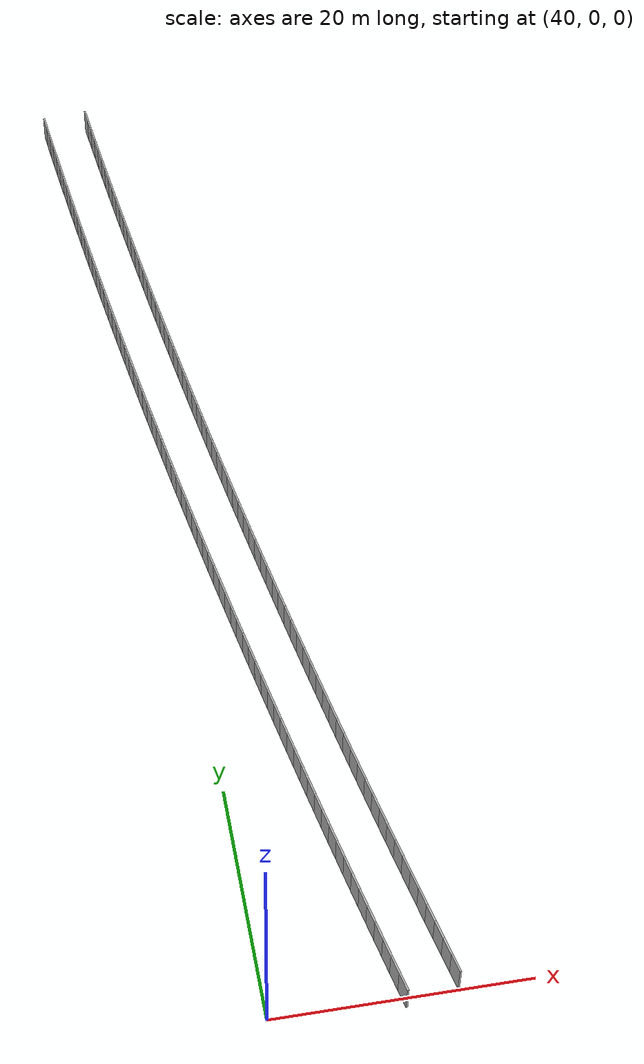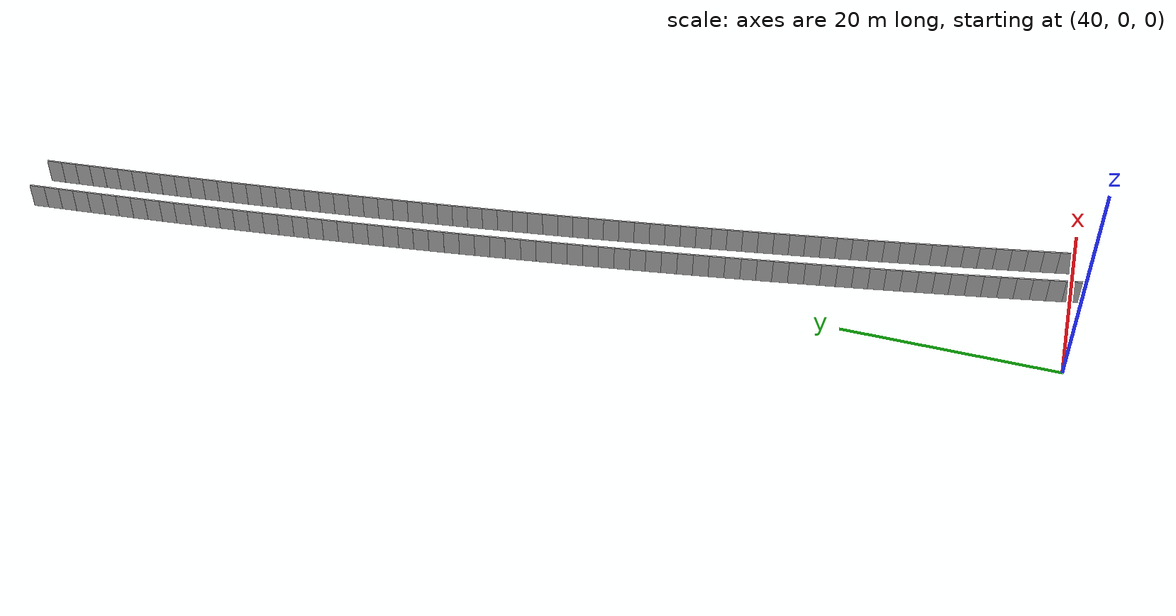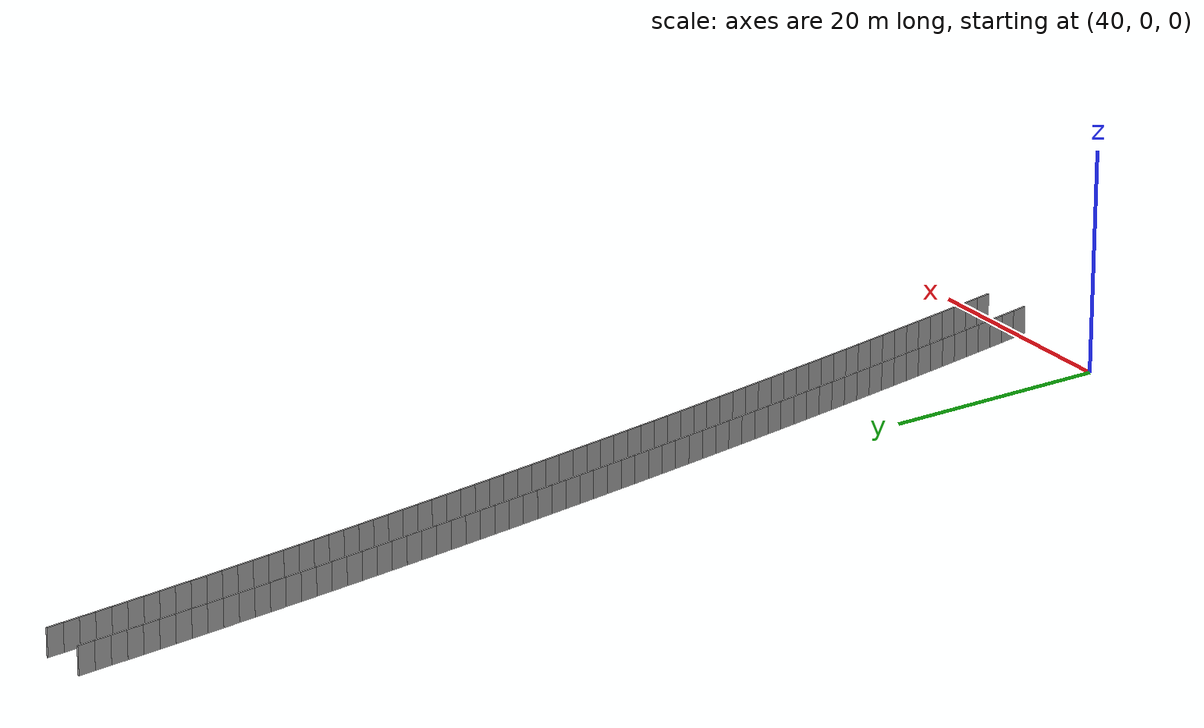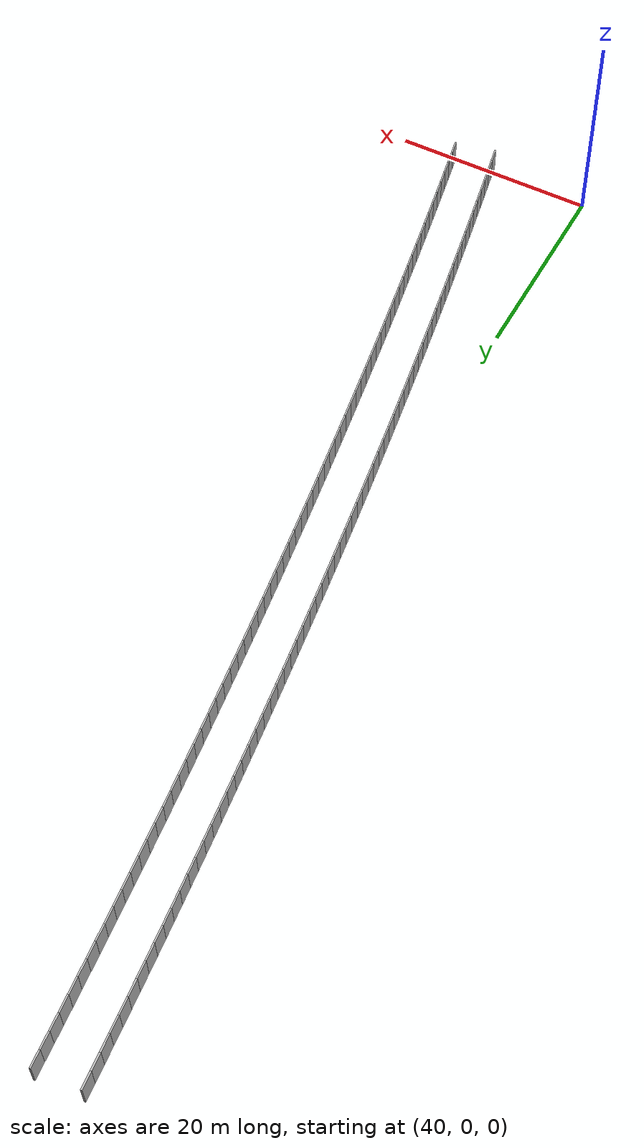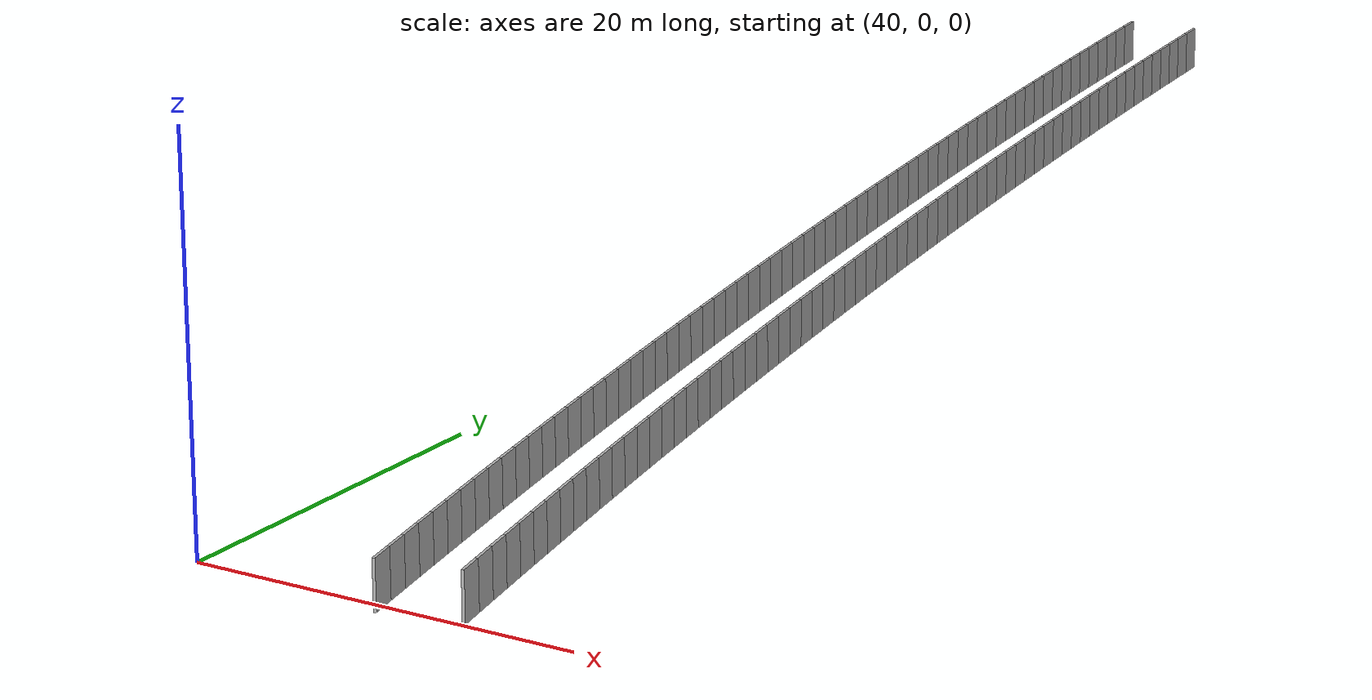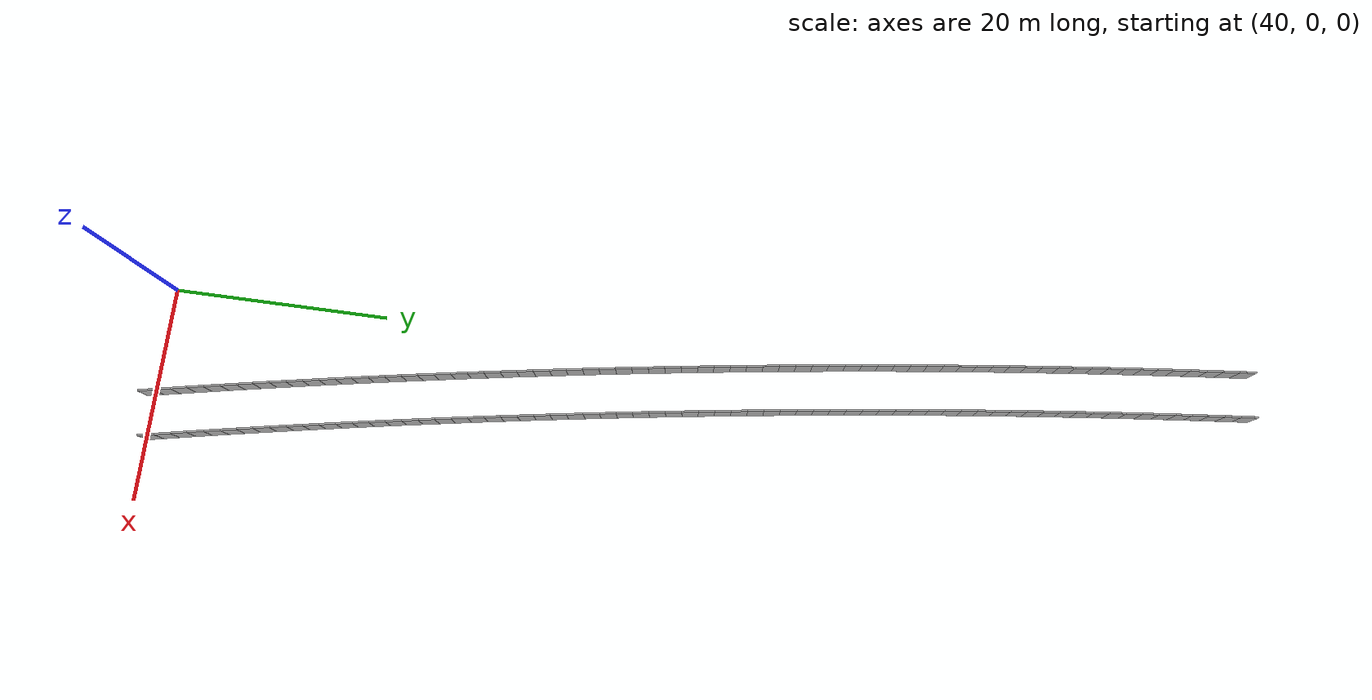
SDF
<?xml version="1.0" ?>
<sdf version="1.6">
  <model name="sps_0111">
    <pose frame="">0 0 0 0 -0 0</pose>
    <static>1</static>
    <self_collide>0</self_collide>
    <allow_auto_disable>0</allow_auto_disable>
    <link name="Wall5310">
      <kinematic>0</kinematic>
      <gravity>1</gravity>
      <self_collide>0</self_collide>
      <collision name="collision">
        <geometry>
          <box>
            <size>1.49644 0.15 2.5</size>
          </box>
        </geometry>
        <pose frame="">0 0 0 0 -0 0</pose>
      </collision>
      <visual name="visual">
        <geometry>
          <box>
            <size>1.49644 0.15 2.5</size>
          </box>
        </geometry>
        <pose frame="">0 0 0 0 -0 0</pose>
        <cast_shadows>1</cast_shadows>
        <transparency>0.0</transparency>
      </visual>
      <pose frame="">38.9795 99.9341 1.25 0 0 -1.47238</pose>
    </link>
    <link name="Wall5311">
      <kinematic>0</kinematic>
      <gravity>1</gravity>
      <self_collide>0</self_collide>
      <collision name="collision">
        <geometry>
          <box>
            <size>1.49667 0.15 2.5</size>
          </box>
        </geometry>
        <pose frame="">0 0 0 0 -0 0</pose>
      </collision>
      <visual name="visual">
        <geometry>
          <box>
            <size>1.49667 0.15 2.5</size>
          </box>
        </geometry>
        <pose frame="">0 0 0 0 -0 0</pose>
        <cast_shadows>1</cast_shadows>
        <transparency>0.0</transparency>
      </visual>
      <pose frame="">39.1278 98.4449 1.25 0 0 -1.4708</pose>
    </link>
    <link name="Wall5312">
      <kinematic>0</kinematic>
      <gravity>1</gravity>
      <self_collide>0</self_collide>
      <collision name="collision">
        <geometry>
          <box>
            <size>1.49649 0.15 2.5</size>
          </box>
        </geometry>
        <pose frame="">0 0 0 0 -0 0</pose>
      </collision>
      <visual name="visual">
        <geometry>
          <box>
            <size>1.49649 0.15 2.5</size>
          </box>
        </geometry>
        <pose frame="">0 0 0 0 -0 0</pose>
        <cast_shadows>1</cast_shadows>
        <transparency>0.0</transparency>
      </visual>
      <pose frame="">39.2784 96.9559 1.25 0 0 -1.46919</pose>
    </link>
    <link name="Wall5313">
      <kinematic>0</kinematic>
      <gravity>1</gravity>
      <self_collide>0</self_collide>
      <collision name="collision">
        <geometry>
          <box>
            <size>1.49653 0.15 2.5</size>
          </box>
        </geometry>
        <pose frame="">0 0 0 0 -0 0</pose>
      </collision>
      <visual name="visual">
        <geometry>
          <box>
            <size>1.49653 0.15 2.5</size>
          </box>
        </geometry>
        <pose frame="">0 0 0 0 -0 0</pose>
        <cast_shadows>1</cast_shadows>
        <transparency>0.0</transparency>
      </visual>
      <pose frame="">39.4313 95.4672 1.25 0 0 -1.46771</pose>
    </link>
    <link name="Wall5314">
      <kinematic>0</kinematic>
      <gravity>1</gravity>
      <self_collide>0</self_collide>
      <collision name="collision">
        <geometry>
          <box>
            <size>1.49644 0.15 2.5</size>
          </box>
        </geometry>
        <pose frame="">0 0 0 0 -0 0</pose>
      </collision>
      <visual name="visual">
        <geometry>
          <box>
            <size>1.49644 0.15 2.5</size>
          </box>
        </geometry>
        <pose frame="">0 0 0 0 -0 0</pose>
        <cast_shadows>1</cast_shadows>
        <transparency>0.0</transparency>
      </visual>
      <pose frame="">39.5866 93.9788 1.25 0 0 -1.46595</pose>
    </link>
    <link name="Wall5315">
      <kinematic>0</kinematic>
      <gravity>1</gravity>
      <self_collide>0</self_collide>
      <collision name="collision">
        <geometry>
          <box>
            <size>1.49666 0.15 2.5</size>
          </box>
        </geometry>
        <pose frame="">0 0 0 0 -0 0</pose>
      </collision>
      <visual name="visual">
        <geometry>
          <box>
            <size>1.49666 0.15 2.5</size>
          </box>
        </geometry>
        <pose frame="">0 0 0 0 -0 0</pose>
        <cast_shadows>1</cast_shadows>
        <transparency>0.0</transparency>
      </visual>
      <pose frame="">39.7443 92.4906 1.25 0 0 -1.46453</pose>
    </link>
    <link name="Wall5316">
      <kinematic>0</kinematic>
      <gravity>1</gravity>
      <self_collide>0</self_collide>
      <collision name="collision">
        <geometry>
          <box>
            <size>1.49648 0.15 2.5</size>
          </box>
        </geometry>
        <pose frame="">0 0 0 0 -0 0</pose>
      </collision>
      <visual name="visual">
        <geometry>
          <box>
            <size>1.49648 0.15 2.5</size>
          </box>
        </geometry>
        <pose frame="">0 0 0 0 -0 0</pose>
        <cast_shadows>1</cast_shadows>
        <transparency>0.0</transparency>
      </visual>
      <pose frame="">39.9041 91.0026 1.25 0 0 -1.46299</pose>
    </link>
    <link name="Wall5317">
      <kinematic>0</kinematic>
      <gravity>1</gravity>
      <self_collide>0</self_collide>
      <collision name="collision">
        <geometry>
          <box>
            <size>1.49656 0.15 2.5</size>
          </box>
        </geometry>
        <pose frame="">0 0 0 0 -0 0</pose>
      </collision>
      <visual name="visual">
        <geometry>
          <box>
            <size>1.49656 0.15 2.5</size>
          </box>
        </geometry>
        <pose frame="">0 0 0 0 -0 0</pose>
        <cast_shadows>1</cast_shadows>
        <transparency>0.0</transparency>
      </visual>
      <pose frame="">40.0663 89.5149 1.25 0 0 -1.4614</pose>
    </link>
    <link name="Wall5318">
      <kinematic>0</kinematic>
      <gravity>1</gravity>
      <self_collide>0</self_collide>
      <collision name="collision">
        <geometry>
          <box>
            <size>1.49642 0.15 2.5</size>
          </box>
        </geometry>
        <pose frame="">0 0 0 0 -0 0</pose>
      </collision>
      <visual name="visual">
        <geometry>
          <box>
            <size>1.49642 0.15 2.5</size>
          </box>
        </geometry>
        <pose frame="">0 0 0 0 -0 0</pose>
        <cast_shadows>1</cast_shadows>
        <transparency>0.0</transparency>
      </visual>
      <pose frame="">40.231 88.0275 1.25 0 0 -1.45963</pose>
    </link>
    <link name="Wall5319">
      <kinematic>0</kinematic>
      <gravity>1</gravity>
      <self_collide>0</self_collide>
      <collision name="collision">
        <geometry>
          <box>
            <size>1.4965 0.15 2.5</size>
          </box>
        </geometry>
        <pose frame="">0 0 0 0 -0 0</pose>
      </collision>
      <visual name="visual">
        <geometry>
          <box>
            <size>1.4965 0.15 2.5</size>
          </box>
        </geometry>
        <pose frame="">0 0 0 0 -0 0</pose>
        <cast_shadows>1</cast_shadows>
        <transparency>0.0</transparency>
      </visual>
      <pose frame="">40.3982 86.5404 1.25 0 0 -1.45803</pose>
    </link>
    <link name="Wall5320">
      <kinematic>0</kinematic>
      <gravity>1</gravity>
      <self_collide>0</self_collide>
      <collision name="collision">
        <geometry>
          <box>
            <size>1.49657 0.15 2.5</size>
          </box>
        </geometry>
        <pose frame="">0 0 0 0 -0 0</pose>
      </collision>
      <visual name="visual">
        <geometry>
          <box>
            <size>1.49657 0.15 2.5</size>
          </box>
        </geometry>
        <pose frame="">0 0 0 0 -0 0</pose>
        <cast_shadows>1</cast_shadows>
        <transparency>0.0</transparency>
      </visual>
      <pose frame="">40.5677 85.0535 1.25 0 0 -1.45656</pose>
    </link>
    <link name="Wall5321">
      <kinematic>0</kinematic>
      <gravity>1</gravity>
      <self_collide>0</self_collide>
      <collision name="collision">
        <geometry>
          <box>
            <size>1.49658 0.15 2.5</size>
          </box>
        </geometry>
        <pose frame="">0 0 0 0 -0 0</pose>
      </collision>
      <visual name="visual">
        <geometry>
          <box>
            <size>1.49658 0.15 2.5</size>
          </box>
        </geometry>
        <pose frame="">0 0 0 0 -0 0</pose>
        <cast_shadows>1</cast_shadows>
        <transparency>0.0</transparency>
      </visual>
      <pose frame="">40.7394 83.5668 1.25 0 0 -1.45508</pose>
    </link>
    <link name="Wall5322">
      <kinematic>0</kinematic>
      <gravity>1</gravity>
      <self_collide>0</self_collide>
      <collision name="collision">
        <geometry>
          <box>
            <size>1.49652 0.15 2.5</size>
          </box>
        </geometry>
        <pose frame="">0 0 0 0 -0 0</pose>
      </collision>
      <visual name="visual">
        <geometry>
          <box>
            <size>1.49652 0.15 2.5</size>
          </box>
        </geometry>
        <pose frame="">0 0 0 0 -0 0</pose>
        <cast_shadows>1</cast_shadows>
        <transparency>0.0</transparency>
      </visual>
      <pose frame="">40.9135 82.0804 1.25 0 0 -1.45331</pose>
    </link>
    <link name="Wall5323">
      <kinematic>0</kinematic>
      <gravity>1</gravity>
      <self_collide>0</self_collide>
      <collision name="collision">
        <geometry>
          <box>
            <size>1.4966 0.15 2.5</size>
          </box>
        </geometry>
        <pose frame="">0 0 0 0 -0 0</pose>
      </collision>
      <visual name="visual">
        <geometry>
          <box>
            <size>1.4966 0.15 2.5</size>
          </box>
        </geometry>
        <pose frame="">0 0 0 0 -0 0</pose>
        <cast_shadows>1</cast_shadows>
        <transparency>0.0</transparency>
      </visual>
      <pose frame="">41.09 80.5943 1.25 0 0 -1.45184</pose>
    </link>
    <link name="Wall5324">
      <kinematic>0</kinematic>
      <gravity>1</gravity>
      <self_collide>0</self_collide>
      <collision name="collision">
        <geometry>
          <box>
            <size>1.49646 0.15 2.5</size>
          </box>
        </geometry>
        <pose frame="">0 0 0 0 -0 0</pose>
      </collision>
      <visual name="visual">
        <geometry>
          <box>
            <size>1.49646 0.15 2.5</size>
          </box>
        </geometry>
        <pose frame="">0 0 0 0 -0 0</pose>
        <cast_shadows>1</cast_shadows>
        <transparency>0.0</transparency>
      </visual>
      <pose frame="">41.2689 79.1085 1.25 0 0 -1.45023</pose>
    </link>
    <link name="Wall5325">
      <kinematic>0</kinematic>
      <gravity>1</gravity>
      <self_collide>0</self_collide>
      <collision name="collision">
        <geometry>
          <box>
            <size>1.49657 0.15 2.5</size>
          </box>
        </geometry>
        <pose frame="">0 0 0 0 -0 0</pose>
      </collision>
      <visual name="visual">
        <geometry>
          <box>
            <size>1.49657 0.15 2.5</size>
          </box>
        </geometry>
        <pose frame="">0 0 0 0 -0 0</pose>
        <cast_shadows>1</cast_shadows>
        <transparency>0.0</transparency>
      </visual>
      <pose frame="">41.4501 77.623 1.25 0 0 -1.44859</pose>
    </link>
    <link name="Wall5326">
      <kinematic>0</kinematic>
      <gravity>1</gravity>
      <self_collide>0</self_collide>
      <collision name="collision">
        <geometry>
          <box>
            <size>1.49643 0.15 2.5</size>
          </box>
        </geometry>
        <pose frame="">0 0 0 0 -0 0</pose>
      </collision>
      <visual name="visual">
        <geometry>
          <box>
            <size>1.49643 0.15 2.5</size>
          </box>
        </geometry>
        <pose frame="">0 0 0 0 -0 0</pose>
        <cast_shadows>1</cast_shadows>
        <transparency>0.0</transparency>
      </visual>
      <pose frame="">41.6337 76.1378 1.25 0 0 -1.44702</pose>
    </link>
    <link name="Wall5327">
      <kinematic>0</kinematic>
      <gravity>1</gravity>
      <self_collide>0</self_collide>
      <collision name="collision">
        <geometry>
          <box>
            <size>1.49653 0.15 2.5</size>
          </box>
        </geometry>
        <pose frame="">0 0 0 0 -0 0</pose>
      </collision>
      <visual name="visual">
        <geometry>
          <box>
            <size>1.49653 0.15 2.5</size>
          </box>
        </geometry>
        <pose frame="">0 0 0 0 -0 0</pose>
        <cast_shadows>1</cast_shadows>
        <transparency>0.0</transparency>
      </visual>
      <pose frame="">41.8195 74.6529 1.25 0 0 -1.44551</pose>
    </link>
    <link name="Wall5328">
      <kinematic>0</kinematic>
      <gravity>1</gravity>
      <self_collide>0</self_collide>
      <collision name="collision">
        <geometry>
          <box>
            <size>1.49659 0.15 2.5</size>
          </box>
        </geometry>
        <pose frame="">0 0 0 0 -0 0</pose>
      </collision>
      <visual name="visual">
        <geometry>
          <box>
            <size>1.49659 0.15 2.5</size>
          </box>
        </geometry>
        <pose frame="">0 0 0 0 -0 0</pose>
        <cast_shadows>1</cast_shadows>
        <transparency>0.0</transparency>
      </visual>
      <pose frame="">42.0077 73.1682 1.25 0 0 -1.44391</pose>
    </link>
    <link name="Wall5329">
      <kinematic>0</kinematic>
      <gravity>1</gravity>
      <self_collide>0</self_collide>
      <collision name="collision">
        <geometry>
          <box>
            <size>1.49657 0.15 2.5</size>
          </box>
        </geometry>
        <pose frame="">0 0 0 0 -0 0</pose>
      </collision>
      <visual name="visual">
        <geometry>
          <box>
            <size>1.49657 0.15 2.5</size>
          </box>
        </geometry>
        <pose frame="">0 0 0 0 -0 0</pose>
        <cast_shadows>1</cast_shadows>
        <transparency>0.0</transparency>
      </visual>
      <pose frame="">42.1982 71.6838 1.25 0 0 -1.44242</pose>
    </link>
    <link name="Wall5330">
      <kinematic>0</kinematic>
      <gravity>1</gravity>
      <self_collide>0</self_collide>
      <collision name="collision">
        <geometry>
          <box>
            <size>1.49642 0.15 2.5</size>
          </box>
        </geometry>
        <pose frame="">0 0 0 0 -0 0</pose>
      </collision>
      <visual name="visual">
        <geometry>
          <box>
            <size>1.49642 0.15 2.5</size>
          </box>
        </geometry>
        <pose frame="">0 0 0 0 -0 0</pose>
        <cast_shadows>1</cast_shadows>
        <transparency>0.0</transparency>
      </visual>
      <pose frame="">42.3911 70.1998 1.25 0 0 -1.44064</pose>
    </link>
    <link name="Wall5331">
      <kinematic>0</kinematic>
      <gravity>1</gravity>
      <self_collide>0</self_collide>
      <collision name="collision">
        <geometry>
          <box>
            <size>1.49655 0.15 2.5</size>
          </box>
        </geometry>
        <pose frame="">0 0 0 0 -0 0</pose>
      </collision>
      <visual name="visual">
        <geometry>
          <box>
            <size>1.49655 0.15 2.5</size>
          </box>
        </geometry>
        <pose frame="">0 0 0 0 -0 0</pose>
        <cast_shadows>1</cast_shadows>
        <transparency>0.0</transparency>
      </visual>
      <pose frame="">42.5865 68.7161 1.25 0 0 -1.43905</pose>
    </link>
    <link name="Wall5332">
      <kinematic>0</kinematic>
      <gravity>1</gravity>
      <self_collide>0</self_collide>
      <collision name="collision">
        <geometry>
          <box>
            <size>1.49648 0.15 2.5</size>
          </box>
        </geometry>
        <pose frame="">0 0 0 0 -0 0</pose>
      </collision>
      <visual name="visual">
        <geometry>
          <box>
            <size>1.49648 0.15 2.5</size>
          </box>
        </geometry>
        <pose frame="">0 0 0 0 -0 0</pose>
        <cast_shadows>1</cast_shadows>
        <transparency>0.0</transparency>
      </visual>
      <pose frame="">42.7842 67.2327 1.25 0 0 -1.43756</pose>
    </link>
    <link name="Wall5333">
      <kinematic>0</kinematic>
      <gravity>1</gravity>
      <self_collide>0</self_collide>
      <collision name="collision">
        <geometry>
          <box>
            <size>1.49662 0.15 2.5</size>
          </box>
        </geometry>
        <pose frame="">0 0 0 0 -0 0</pose>
      </collision>
      <visual name="visual">
        <geometry>
          <box>
            <size>1.49662 0.15 2.5</size>
          </box>
        </geometry>
        <pose frame="">0 0 0 0 -0 0</pose>
        <cast_shadows>1</cast_shadows>
        <transparency>0.0</transparency>
      </visual>
      <pose frame="">42.9842 65.7496 1.25 0 0 -1.43593</pose>
    </link>
    <link name="Wall5334">
      <kinematic>0</kinematic>
      <gravity>1</gravity>
      <self_collide>0</self_collide>
      <collision name="collision">
        <geometry>
          <box>
            <size>1.49649 0.15 2.5</size>
          </box>
        </geometry>
        <pose frame="">0 0 0 0 -0 0</pose>
      </collision>
      <visual name="visual">
        <geometry>
          <box>
            <size>1.49649 0.15 2.5</size>
          </box>
        </geometry>
        <pose frame="">0 0 0 0 -0 0</pose>
        <cast_shadows>1</cast_shadows>
        <transparency>0.0</transparency>
      </visual>
      <pose frame="">43.1865 64.2668 1.25 0 0 -1.43448</pose>
    </link>
    <link name="Wall5335">
      <kinematic>0</kinematic>
      <gravity>1</gravity>
      <self_collide>0</self_collide>
      <collision name="collision">
        <geometry>
          <box>
            <size>1.49643 0.15 2.5</size>
          </box>
        </geometry>
        <pose frame="">0 0 0 0 -0 0</pose>
      </collision>
      <visual name="visual">
        <geometry>
          <box>
            <size>1.49643 0.15 2.5</size>
          </box>
        </geometry>
        <pose frame="">0 0 0 0 -0 0</pose>
        <cast_shadows>1</cast_shadows>
        <transparency>0.0</transparency>
      </visual>
      <pose frame="">43.3913 62.7844 1.25 0 0 -1.43266</pose>
    </link>
    <link name="Wall5336">
      <kinematic>0</kinematic>
      <gravity>1</gravity>
      <self_collide>0</self_collide>
      <collision name="collision">
        <geometry>
          <box>
            <size>1.49651 0.15 2.5</size>
          </box>
        </geometry>
        <pose frame="">0 0 0 0 -0 0</pose>
      </collision>
      <visual name="visual">
        <geometry>
          <box>
            <size>1.49651 0.15 2.5</size>
          </box>
        </geometry>
        <pose frame="">0 0 0 0 -0 0</pose>
        <cast_shadows>1</cast_shadows>
        <transparency>0.0</transparency>
      </visual>
      <pose frame="">43.5983 61.3023 1.25 0 0 -1.43139</pose>
    </link>
    <link name="Wall5337">
      <kinematic>0</kinematic>
      <gravity>1</gravity>
      <self_collide>0</self_collide>
      <collision name="collision">
        <geometry>
          <box>
            <size>1.49653 0.15 2.5</size>
          </box>
        </geometry>
        <pose frame="">0 0 0 0 -0 0</pose>
      </collision>
      <visual name="visual">
        <geometry>
          <box>
            <size>1.49653 0.15 2.5</size>
          </box>
        </geometry>
        <pose frame="">0 0 0 0 -0 0</pose>
        <cast_shadows>1</cast_shadows>
        <transparency>0.0</transparency>
      </visual>
      <pose frame="">43.8075 59.8205 1.25 0 0 -1.42958</pose>
    </link>
    <link name="Wall5338">
      <kinematic>0</kinematic>
      <gravity>1</gravity>
      <self_collide>0</self_collide>
      <collision name="collision">
        <geometry>
          <box>
            <size>1.49659 0.15 2.5</size>
          </box>
        </geometry>
        <pose frame="">0 0 0 0 -0 0</pose>
      </collision>
      <visual name="visual">
        <geometry>
          <box>
            <size>1.49659 0.15 2.5</size>
          </box>
        </geometry>
        <pose frame="">0 0 0 0 -0 0</pose>
        <cast_shadows>1</cast_shadows>
        <transparency>0.0</transparency>
      </visual>
      <pose frame="">44.0192 58.339 1.25 0 0 -1.42814</pose>
    </link>
    <link name="Wall5339">
      <kinematic>0</kinematic>
      <gravity>1</gravity>
      <self_collide>0</self_collide>
      <collision name="collision">
        <geometry>
          <box>
            <size>1.49633 0.15 2.5</size>
          </box>
        </geometry>
        <pose frame="">0 0 0 0 -0 0</pose>
      </collision>
      <visual name="visual">
        <geometry>
          <box>
            <size>1.49633 0.15 2.5</size>
          </box>
        </geometry>
        <pose frame="">0 0 0 0 -0 0</pose>
        <cast_shadows>1</cast_shadows>
        <transparency>0.0</transparency>
      </visual>
      <pose frame="">44.2332 56.8579 1.25 0 0 -1.42647</pose>
    </link>
    <link name="Wall5340">
      <kinematic>0</kinematic>
      <gravity>1</gravity>
      <self_collide>0</self_collide>
      <collision name="collision">
        <geometry>
          <box>
            <size>1.49677 0.15 2.5</size>
          </box>
        </geometry>
        <pose frame="">0 0 0 0 -0 0</pose>
      </collision>
      <visual name="visual">
        <geometry>
          <box>
            <size>1.49677 0.15 2.5</size>
          </box>
        </geometry>
        <pose frame="">0 0 0 0 -0 0</pose>
        <cast_shadows>1</cast_shadows>
        <transparency>0.0</transparency>
      </visual>
      <pose frame="">44.4498 55.3771 1.25 0 0 -1.42474</pose>
    </link>
    <link name="Wall5341">
      <kinematic>0</kinematic>
      <gravity>1</gravity>
      <self_collide>0</self_collide>
      <collision name="collision">
        <geometry>
          <box>
            <size>1.49642 0.15 2.5</size>
          </box>
        </geometry>
        <pose frame="">0 0 0 0 -0 0</pose>
      </collision>
      <visual name="visual">
        <geometry>
          <box>
            <size>1.49642 0.15 2.5</size>
          </box>
        </geometry>
        <pose frame="">0 0 0 0 -0 0</pose>
        <cast_shadows>1</cast_shadows>
        <transparency>0.0</transparency>
      </visual>
      <pose frame="">44.6687 53.8966 1.25 0 0 -1.42326</pose>
    </link>
    <link name="Wall5342">
      <kinematic>0</kinematic>
      <gravity>1</gravity>
      <self_collide>0</self_collide>
      <collision name="collision">
        <geometry>
          <box>
            <size>1.49663 0.15 2.5</size>
          </box>
        </geometry>
        <pose frame="">0 0 0 0 -0 0</pose>
      </collision>
      <visual name="visual">
        <geometry>
          <box>
            <size>1.49663 0.15 2.5</size>
          </box>
        </geometry>
        <pose frame="">0 0 0 0 -0 0</pose>
        <cast_shadows>1</cast_shadows>
        <transparency>0.0</transparency>
      </visual>
      <pose frame="">44.8898 52.4165 1.25 0 0 -1.42176</pose>
    </link>
    <link name="Wall5343">
      <kinematic>0</kinematic>
      <gravity>1</gravity>
      <self_collide>0</self_collide>
      <collision name="collision">
        <geometry>
          <box>
            <size>1.49632 0.15 2.5</size>
          </box>
        </geometry>
        <pose frame="">0 0 0 0 -0 0</pose>
      </collision>
      <visual name="visual">
        <geometry>
          <box>
            <size>1.49632 0.15 2.5</size>
          </box>
        </geometry>
        <pose frame="">0 0 0 0 -0 0</pose>
        <cast_shadows>1</cast_shadows>
        <transparency>0.0</transparency>
      </visual>
      <pose frame="">45.1132 50.9368 1.25 0 0 -1.42012</pose>
    </link>
    <link name="Wall5344">
      <kinematic>0</kinematic>
      <gravity>1</gravity>
      <self_collide>0</self_collide>
      <collision name="collision">
        <geometry>
          <box>
            <size>1.4965 0.15 2.5</size>
          </box>
        </geometry>
        <pose frame="">0 0 0 0 -0 0</pose>
      </collision>
      <visual name="visual">
        <geometry>
          <box>
            <size>1.4965 0.15 2.5</size>
          </box>
        </geometry>
        <pose frame="">0 0 0 0 -0 0</pose>
        <cast_shadows>1</cast_shadows>
        <transparency>0.0</transparency>
      </visual>
      <pose frame="">45.339 49.4575 1.25 0 0 -1.41853</pose>
    </link>
    <link name="Wall5345">
      <kinematic>0</kinematic>
      <gravity>1</gravity>
      <self_collide>0</self_collide>
      <collision name="collision">
        <geometry>
          <box>
            <size>1.4965 0.15 2.5</size>
          </box>
        </geometry>
        <pose frame="">0 0 0 0 -0 0</pose>
      </collision>
      <visual name="visual">
        <geometry>
          <box>
            <size>1.4965 0.15 2.5</size>
          </box>
        </geometry>
        <pose frame="">0 0 0 0 -0 0</pose>
        <cast_shadows>1</cast_shadows>
        <transparency>0.0</transparency>
      </visual>
      <pose frame="">45.5672 47.9785 1.25 0 0 -1.41692</pose>
    </link>
    <link name="Wall5346">
      <kinematic>0</kinematic>
      <gravity>1</gravity>
      <self_collide>0</self_collide>
      <collision name="collision">
        <geometry>
          <box>
            <size>1.49664 0.15 2.5</size>
          </box>
        </geometry>
        <pose frame="">0 0 0 0 -0 0</pose>
      </collision>
      <visual name="visual">
        <geometry>
          <box>
            <size>1.49664 0.15 2.5</size>
          </box>
        </geometry>
        <pose frame="">0 0 0 0 -0 0</pose>
        <cast_shadows>1</cast_shadows>
        <transparency>0.0</transparency>
      </visual>
      <pose frame="">45.7978 46.4998 1.25 0 0 -1.41528</pose>
    </link>
    <link name="Wall5347">
      <kinematic>0</kinematic>
      <gravity>1</gravity>
      <self_collide>0</self_collide>
      <collision name="collision">
        <geometry>
          <box>
            <size>1.49644 0.15 2.5</size>
          </box>
        </geometry>
        <pose frame="">0 0 0 0 -0 0</pose>
      </collision>
      <visual name="visual">
        <geometry>
          <box>
            <size>1.49644 0.15 2.5</size>
          </box>
        </geometry>
        <pose frame="">0 0 0 0 -0 0</pose>
        <cast_shadows>1</cast_shadows>
        <transparency>0.0</transparency>
      </visual>
      <pose frame="">46.0307 45.0215 1.25 0 0 -1.41377</pose>
    </link>
    <link name="Wall5348">
      <kinematic>0</kinematic>
      <gravity>1</gravity>
      <self_collide>0</self_collide>
      <collision name="collision">
        <geometry>
          <box>
            <size>1.49657 0.15 2.5</size>
          </box>
        </geometry>
        <pose frame="">0 0 0 0 -0 0</pose>
      </collision>
      <visual name="visual">
        <geometry>
          <box>
            <size>1.49657 0.15 2.5</size>
          </box>
        </geometry>
        <pose frame="">0 0 0 0 -0 0</pose>
        <cast_shadows>1</cast_shadows>
        <transparency>0.0</transparency>
      </visual>
      <pose frame="">46.2659 43.5436 1.25 0 0 -1.41218</pose>
    </link>
    <link name="Wall5349">
      <kinematic>0</kinematic>
      <gravity>1</gravity>
      <self_collide>0</self_collide>
      <collision name="collision">
        <geometry>
          <box>
            <size>1.49638 0.15 2.5</size>
          </box>
        </geometry>
        <pose frame="">0 0 0 0 -0 0</pose>
      </collision>
      <visual name="visual">
        <geometry>
          <box>
            <size>1.49638 0.15 2.5</size>
          </box>
        </geometry>
        <pose frame="">0 0 0 0 -0 0</pose>
        <cast_shadows>1</cast_shadows>
        <transparency>0.0</transparency>
      </visual>
      <pose frame="">46.5033 42.0661 1.25 0 0 -1.41067</pose>
    </link>
    <link name="Wall5350">
      <kinematic>0</kinematic>
      <gravity>1</gravity>
      <self_collide>0</self_collide>
      <collision name="collision">
        <geometry>
          <box>
            <size>1.49653 0.15 2.5</size>
          </box>
        </geometry>
        <pose frame="">0 0 0 0 -0 0</pose>
      </collision>
      <visual name="visual">
        <geometry>
          <box>
            <size>1.49653 0.15 2.5</size>
          </box>
        </geometry>
        <pose frame="">0 0 0 0 -0 0</pose>
        <cast_shadows>1</cast_shadows>
        <transparency>0.0</transparency>
      </visual>
      <pose frame="">46.7432 40.589 1.25 0 0 -1.40903</pose>
    </link>
    <link name="Wall5351">
      <kinematic>0</kinematic>
      <gravity>1</gravity>
      <self_collide>0</self_collide>
      <collision name="collision">
        <geometry>
          <box>
            <size>1.49673 0.15 2.5</size>
          </box>
        </geometry>
        <pose frame="">0 0 0 0 -0 0</pose>
      </collision>
      <visual name="visual">
        <geometry>
          <box>
            <size>1.49673 0.15 2.5</size>
          </box>
        </geometry>
        <pose frame="">0 0 0 0 -0 0</pose>
        <cast_shadows>1</cast_shadows>
        <transparency>0.0</transparency>
      </visual>
      <pose frame="">46.9854 39.1121 1.25 0 0 -1.40744</pose>
    </link>
    <link name="Wall5352">
      <kinematic>0</kinematic>
      <gravity>1</gravity>
      <self_collide>0</self_collide>
      <collision name="collision">
        <geometry>
          <box>
            <size>1.49649 0.15 2.5</size>
          </box>
        </geometry>
        <pose frame="">0 0 0 0 -0 0</pose>
      </collision>
      <visual name="visual">
        <geometry>
          <box>
            <size>1.49649 0.15 2.5</size>
          </box>
        </geometry>
        <pose frame="">0 0 0 0 -0 0</pose>
        <cast_shadows>1</cast_shadows>
        <transparency>0.0</transparency>
      </visual>
      <pose frame="">47.2299 37.6356 1.25 0 0 -1.40593</pose>
    </link>
    <link name="Wall5353">
      <kinematic>0</kinematic>
      <gravity>1</gravity>
      <self_collide>0</self_collide>
      <collision name="collision">
        <geometry>
          <box>
            <size>1.49646 0.15 2.5</size>
          </box>
        </geometry>
        <pose frame="">0 0 0 0 -0 0</pose>
      </collision>
      <visual name="visual">
        <geometry>
          <box>
            <size>1.49646 0.15 2.5</size>
          </box>
        </geometry>
        <pose frame="">0 0 0 0 -0 0</pose>
        <cast_shadows>1</cast_shadows>
        <transparency>0.0</transparency>
      </visual>
      <pose frame="">47.4767 36.1596 1.25 0 0 -1.40431</pose>
    </link>
    <link name="Wall5354">
      <kinematic>0</kinematic>
      <gravity>1</gravity>
      <self_collide>0</self_collide>
      <collision name="collision">
        <geometry>
          <box>
            <size>1.49649 0.15 2.5</size>
          </box>
        </geometry>
        <pose frame="">0 0 0 0 -0 0</pose>
      </collision>
      <visual name="visual">
        <geometry>
          <box>
            <size>1.49649 0.15 2.5</size>
          </box>
        </geometry>
        <pose frame="">0 0 0 0 -0 0</pose>
        <cast_shadows>1</cast_shadows>
        <transparency>0.0</transparency>
      </visual>
      <pose frame="">47.7259 34.684 1.25 0 0 -1.4027</pose>
    </link>
    <link name="Wall5355">
      <kinematic>0</kinematic>
      <gravity>1</gravity>
      <self_collide>0</self_collide>
      <collision name="collision">
        <geometry>
          <box>
            <size>1.49654 0.15 2.5</size>
          </box>
        </geometry>
        <pose frame="">0 0 0 0 -0 0</pose>
      </collision>
      <visual name="visual">
        <geometry>
          <box>
            <size>1.49654 0.15 2.5</size>
          </box>
        </geometry>
        <pose frame="">0 0 0 0 -0 0</pose>
        <cast_shadows>1</cast_shadows>
        <transparency>0.0</transparency>
      </visual>
      <pose frame="">47.9774 33.2088 1.25 0 0 -1.40105</pose>
    </link>
    <link name="Wall5356">
      <kinematic>0</kinematic>
      <gravity>1</gravity>
      <self_collide>0</self_collide>
      <collision name="collision">
        <geometry>
          <box>
            <size>1.49647 0.15 2.5</size>
          </box>
        </geometry>
        <pose frame="">0 0 0 0 -0 0</pose>
      </collision>
      <visual name="visual">
        <geometry>
          <box>
            <size>1.49647 0.15 2.5</size>
          </box>
        </geometry>
        <pose frame="">0 0 0 0 -0 0</pose>
        <cast_shadows>1</cast_shadows>
        <transparency>0.0</transparency>
      </visual>
      <pose frame="">48.2314 31.734 1.25 0 0 -1.39943</pose>
    </link>
    <link name="Wall5357">
      <kinematic>0</kinematic>
      <gravity>1</gravity>
      <self_collide>0</self_collide>
      <collision name="collision">
        <geometry>
          <box>
            <size>1.49655 0.15 2.5</size>
          </box>
        </geometry>
        <pose frame="">0 0 0 0 -0 0</pose>
      </collision>
      <visual name="visual">
        <geometry>
          <box>
            <size>1.49655 0.15 2.5</size>
          </box>
        </geometry>
        <pose frame="">0 0 0 0 -0 0</pose>
        <cast_shadows>1</cast_shadows>
        <transparency>0.0</transparency>
      </visual>
      <pose frame="">48.4878 30.2596 1.25 0 0 -1.39791</pose>
    </link>
    <link name="Wall5358">
      <kinematic>0</kinematic>
      <gravity>1</gravity>
      <self_collide>0</self_collide>
      <collision name="collision">
        <geometry>
          <box>
            <size>1.49647 0.15 2.5</size>
          </box>
        </geometry>
        <pose frame="">0 0 0 0 -0 0</pose>
      </collision>
      <visual name="visual">
        <geometry>
          <box>
            <size>1.49647 0.15 2.5</size>
          </box>
        </geometry>
        <pose frame="">0 0 0 0 -0 0</pose>
        <cast_shadows>1</cast_shadows>
        <transparency>0.0</transparency>
      </visual>
      <pose frame="">48.7464 28.7856 1.25 0 0 -1.39633</pose>
    </link>
    <link name="Wall5359">
      <kinematic>0</kinematic>
      <gravity>1</gravity>
      <self_collide>0</self_collide>
      <collision name="collision">
        <geometry>
          <box>
            <size>1.49657 0.15 2.5</size>
          </box>
        </geometry>
        <pose frame="">0 0 0 0 -0 0</pose>
      </collision>
      <visual name="visual">
        <geometry>
          <box>
            <size>1.49657 0.15 2.5</size>
          </box>
        </geometry>
        <pose frame="">0 0 0 0 -0 0</pose>
        <cast_shadows>1</cast_shadows>
        <transparency>0.0</transparency>
      </visual>
      <pose frame="">49.0073 27.312 1.25 0 0 -1.39481</pose>
    </link>
    <link name="Wall5360">
      <kinematic>0</kinematic>
      <gravity>1</gravity>
      <self_collide>0</self_collide>
      <collision name="collision">
        <geometry>
          <box>
            <size>1.4965 0.15 2.5</size>
          </box>
        </geometry>
        <pose frame="">0 0 0 0 -0 0</pose>
      </collision>
      <visual name="visual">
        <geometry>
          <box>
            <size>1.4965 0.15 2.5</size>
          </box>
        </geometry>
        <pose frame="">0 0 0 0 -0 0</pose>
        <cast_shadows>1</cast_shadows>
        <transparency>0.0</transparency>
      </visual>
      <pose frame="">49.2705 25.8388 1.25 0 0 -1.39318</pose>
    </link>
    <link name="Wall5361">
      <kinematic>0</kinematic>
      <gravity>1</gravity>
      <self_collide>0</self_collide>
      <collision name="collision">
        <geometry>
          <box>
            <size>1.49653 0.15 2.5</size>
          </box>
        </geometry>
        <pose frame="">0 0 0 0 -0 0</pose>
      </collision>
      <visual name="visual">
        <geometry>
          <box>
            <size>1.49653 0.15 2.5</size>
          </box>
        </geometry>
        <pose frame="">0 0 0 0 -0 0</pose>
        <cast_shadows>1</cast_shadows>
        <transparency>0.0</transparency>
      </visual>
      <pose frame="">49.536 24.366 1.25 0 0 -1.39169</pose>
    </link>
    <link name="Wall5362">
      <kinematic>0</kinematic>
      <gravity>1</gravity>
      <self_collide>0</self_collide>
      <collision name="collision">
        <geometry>
          <box>
            <size>1.49642 0.15 2.5</size>
          </box>
        </geometry>
        <pose frame="">0 0 0 0 -0 0</pose>
      </collision>
      <visual name="visual">
        <geometry>
          <box>
            <size>1.49642 0.15 2.5</size>
          </box>
        </geometry>
        <pose frame="">0 0 0 0 -0 0</pose>
        <cast_shadows>1</cast_shadows>
        <transparency>0.0</transparency>
      </visual>
      <pose frame="">49.8038 22.8937 1.25 0 0 -1.39006</pose>
    </link>
    <link name="Wall5363">
      <kinematic>0</kinematic>
      <gravity>1</gravity>
      <self_collide>0</self_collide>
      <collision name="collision">
        <geometry>
          <box>
            <size>1.49634 0.15 2.5</size>
          </box>
        </geometry>
        <pose frame="">0 0 0 0 -0 0</pose>
      </collision>
      <visual name="visual">
        <geometry>
          <box>
            <size>1.49634 0.15 2.5</size>
          </box>
        </geometry>
        <pose frame="">0 0 0 0 -0 0</pose>
        <cast_shadows>1</cast_shadows>
        <transparency>0.0</transparency>
      </visual>
      <pose frame="">50.0738 21.4219 1.25 0 0 -1.38856</pose>
    </link>
    <link name="Wall5364">
      <kinematic>0</kinematic>
      <gravity>1</gravity>
      <self_collide>0</self_collide>
      <collision name="collision">
        <geometry>
          <box>
            <size>1.49645 0.15 2.5</size>
          </box>
        </geometry>
        <pose frame="">0 0 0 0 -0 0</pose>
      </collision>
      <visual name="visual">
        <geometry>
          <box>
            <size>1.49645 0.15 2.5</size>
          </box>
        </geometry>
        <pose frame="">0 0 0 0 -0 0</pose>
        <cast_shadows>1</cast_shadows>
        <transparency>0.0</transparency>
      </visual>
      <pose frame="">50.3463 19.9505 1.25 0 0 -1.38679</pose>
    </link>
    <link name="Wall5365">
      <kinematic>0</kinematic>
      <gravity>1</gravity>
      <self_collide>0</self_collide>
      <collision name="collision">
        <geometry>
          <box>
            <size>1.4965 0.15 2.5</size>
          </box>
        </geometry>
        <pose frame="">0 0 0 0 -0 0</pose>
      </collision>
      <visual name="visual">
        <geometry>
          <box>
            <size>1.4965 0.15 2.5</size>
          </box>
        </geometry>
        <pose frame="">0 0 0 0 -0 0</pose>
        <cast_shadows>1</cast_shadows>
        <transparency>0.0</transparency>
      </visual>
      <pose frame="">50.6212 18.4795 1.25 0 0 -1.3853</pose>
    </link>
    <link name="Wall5366">
      <kinematic>0</kinematic>
      <gravity>1</gravity>
      <self_collide>0</self_collide>
      <collision name="collision">
        <geometry>
          <box>
            <size>1.49656 0.15 2.5</size>
          </box>
        </geometry>
        <pose frame="">0 0 0 0 -0 0</pose>
      </collision>
      <visual name="visual">
        <geometry>
          <box>
            <size>1.49656 0.15 2.5</size>
          </box>
        </geometry>
        <pose frame="">0 0 0 0 -0 0</pose>
        <cast_shadows>1</cast_shadows>
        <transparency>0.0</transparency>
      </visual>
      <pose frame="">50.8986 17.0089 1.25 0 0 -1.38353</pose>
    </link>
    <link name="Wall5367">
      <kinematic>0</kinematic>
      <gravity>1</gravity>
      <self_collide>0</self_collide>
      <collision name="collision">
        <geometry>
          <box>
            <size>1.49657 0.15 2.5</size>
          </box>
        </geometry>
        <pose frame="">0 0 0 0 -0 0</pose>
      </collision>
      <visual name="visual">
        <geometry>
          <box>
            <size>1.49657 0.15 2.5</size>
          </box>
        </geometry>
        <pose frame="">0 0 0 0 -0 0</pose>
        <cast_shadows>1</cast_shadows>
        <transparency>0.0</transparency>
      </visual>
      <pose frame="">51.1782 15.5387 1.25 0 0 -1.3822</pose>
    </link>
    <link name="Wall5368">
      <kinematic>0</kinematic>
      <gravity>1</gravity>
      <self_collide>0</self_collide>
      <collision name="collision">
        <geometry>
          <box>
            <size>1.4964 0.15 2.5</size>
          </box>
        </geometry>
        <pose frame="">0 0 0 0 -0 0</pose>
      </collision>
      <visual name="visual">
        <geometry>
          <box>
            <size>1.4964 0.15 2.5</size>
          </box>
        </geometry>
        <pose frame="">0 0 0 0 -0 0</pose>
        <cast_shadows>1</cast_shadows>
        <transparency>0.0</transparency>
      </visual>
      <pose frame="">51.46 14.069 1.25 0 0 -1.38039</pose>
    </link>
    <link name="Wall5369">
      <kinematic>0</kinematic>
      <gravity>1</gravity>
      <self_collide>0</self_collide>
      <collision name="collision">
        <geometry>
          <box>
            <size>1.4967 0.15 2.5</size>
          </box>
        </geometry>
        <pose frame="">0 0 0 0 -0 0</pose>
      </collision>
      <visual name="visual">
        <geometry>
          <box>
            <size>1.4967 0.15 2.5</size>
          </box>
        </geometry>
        <pose frame="">0 0 0 0 -0 0</pose>
        <cast_shadows>1</cast_shadows>
        <transparency>0.0</transparency>
      </visual>
      <pose frame="">51.7443 12.5997 1.25 0 0 -1.37894</pose>
    </link>
    <link name="Wall5370">
      <kinematic>0</kinematic>
      <gravity>1</gravity>
      <self_collide>0</self_collide>
      <collision name="collision">
        <geometry>
          <box>
            <size>1.49646 0.15 2.5</size>
          </box>
        </geometry>
        <pose frame="">0 0 0 0 -0 0</pose>
      </collision>
      <visual name="visual">
        <geometry>
          <box>
            <size>1.49646 0.15 2.5</size>
          </box>
        </geometry>
        <pose frame="">0 0 0 0 -0 0</pose>
        <cast_shadows>1</cast_shadows>
        <transparency>0.0</transparency>
      </visual>
      <pose frame="">52.0308 11.1308 1.25 0 0 -1.37741</pose>
    </link>
    <link name="Wall5371">
      <kinematic>0</kinematic>
      <gravity>1</gravity>
      <self_collide>0</self_collide>
      <collision name="collision">
        <geometry>
          <box>
            <size>1.49657 0.15 2.5</size>
          </box>
        </geometry>
        <pose frame="">0 0 0 0 -0 0</pose>
      </collision>
      <visual name="visual">
        <geometry>
          <box>
            <size>1.49657 0.15 2.5</size>
          </box>
        </geometry>
        <pose frame="">0 0 0 0 -0 0</pose>
        <cast_shadows>1</cast_shadows>
        <transparency>0.0</transparency>
      </visual>
      <pose frame="">52.3197 9.6624 1.25 0 0 -1.37576</pose>
    </link>
    <link name="Wall5372">
      <kinematic>0</kinematic>
      <gravity>1</gravity>
      <self_collide>0</self_collide>
      <collision name="collision">
        <geometry>
          <box>
            <size>1.49667 0.15 2.5</size>
          </box>
        </geometry>
        <pose frame="">0 0 0 0 -0 0</pose>
      </collision>
      <visual name="visual">
        <geometry>
          <box>
            <size>1.49667 0.15 2.5</size>
          </box>
        </geometry>
        <pose frame="">0 0 0 0 -0 0</pose>
        <cast_shadows>1</cast_shadows>
        <transparency>0.0</transparency>
      </visual>
      <pose frame="">52.6109 8.19438 1.25 0 0 -1.37419</pose>
    </link>
    <link name="Wall5373">
      <kinematic>0</kinematic>
      <gravity>1</gravity>
      <self_collide>0</self_collide>
      <collision name="collision">
        <geometry>
          <box>
            <size>1.49649 0.15 2.5</size>
          </box>
        </geometry>
        <pose frame="">0 0 0 0 -0 0</pose>
      </collision>
      <visual name="visual">
        <geometry>
          <box>
            <size>1.49649 0.15 2.5</size>
          </box>
        </geometry>
        <pose frame="">0 0 0 0 -0 0</pose>
        <cast_shadows>1</cast_shadows>
        <transparency>0.0</transparency>
      </visual>
      <pose frame="">52.9044 6.72688 1.25 0 0 -1.3725</pose>
    </link>
    <link name="Wall5374">
      <kinematic>0</kinematic>
      <gravity>1</gravity>
      <self_collide>0</self_collide>
      <collision name="collision">
        <geometry>
          <box>
            <size>1.49656 0.15 2.5</size>
          </box>
        </geometry>
        <pose frame="">0 0 0 0 -0 0</pose>
      </collision>
      <visual name="visual">
        <geometry>
          <box>
            <size>1.49656 0.15 2.5</size>
          </box>
        </geometry>
        <pose frame="">0 0 0 0 -0 0</pose>
        <cast_shadows>1</cast_shadows>
        <transparency>0.0</transparency>
      </visual>
      <pose frame="">53.2003 5.2599 1.25 0 0 -1.37102</pose>
    </link>
    <link name="Wall5375">
      <kinematic>0</kinematic>
      <gravity>1</gravity>
      <self_collide>0</self_collide>
      <collision name="collision">
        <geometry>
          <box>
            <size>1.4964 0.15 2.5</size>
          </box>
        </geometry>
        <pose frame="">0 0 0 0 -0 0</pose>
      </collision>
      <visual name="visual">
        <geometry>
          <box>
            <size>1.4964 0.15 2.5</size>
          </box>
        </geometry>
        <pose frame="">0 0 0 0 -0 0</pose>
        <cast_shadows>1</cast_shadows>
        <transparency>0.0</transparency>
      </visual>
      <pose frame="">53.4984 3.79341 1.25 0 0 -1.3695</pose>
    </link>
    <link name="Wall5376">
      <kinematic>0</kinematic>
      <gravity>1</gravity>
      <self_collide>0</self_collide>
      <collision name="collision">
        <geometry>
          <box>
            <size>1.49639 0.15 2.5</size>
          </box>
        </geometry>
        <pose frame="">0 0 0 0 -0 0</pose>
      </collision>
      <visual name="visual">
        <geometry>
          <box>
            <size>1.49639 0.15 2.5</size>
          </box>
        </geometry>
        <pose frame="">0 0 0 0 -0 0</pose>
        <cast_shadows>1</cast_shadows>
        <transparency>0.0</transparency>
      </visual>
      <pose frame="">53.7989 2.3275 1.25 0 0 -1.36771</pose>
    </link>
    <link name="Wall5377">
      <kinematic>0</kinematic>
      <gravity>1</gravity>
      <self_collide>0</self_collide>
      <collision name="collision">
        <geometry>
          <box>
            <size>1.4966 0.15 2.5</size>
          </box>
        </geometry>
        <pose frame="">0 0 0 0 -0 0</pose>
      </collision>
      <visual name="visual">
        <geometry>
          <box>
            <size>1.4966 0.15 2.5</size>
          </box>
        </geometry>
        <pose frame="">0 0 0 0 -0 0</pose>
        <cast_shadows>1</cast_shadows>
        <transparency>0.0</transparency>
      </visual>
      <pose frame="">54.1019 0.861983 1.25 0 0 -1.36623</pose>
    </link>
    <link name="Wall7106">
      <kinematic>0</kinematic>
      <gravity>1</gravity>
      <self_collide>0</self_collide>
      <collision name="collision">
        <geometry>
          <box>
            <size>1.50305 0.15 2.5</size>
          </box>
        </geometry>
        <pose frame="">0 0 0 0 -0 0</pose>
      </collision>
      <visual name="visual">
        <geometry>
          <box>
            <size>1.50305 0.15 2.5</size>
          </box>
        </geometry>
        <pose frame="">0 0 0 0 -0 0</pose>
        <cast_shadows>1</cast_shadows>
        <transparency>0.0</transparency>
      </visual>
      <pose frame="">34.8603 99.5272 1.25 0 0 -1.47245</pose>
    </link>
    <link name="Wall7107">
      <kinematic>0</kinematic>
      <gravity>1</gravity>
      <self_collide>0</self_collide>
      <collision name="collision">
        <geometry>
          <box>
            <size>1.50313 0.15 2.5</size>
          </box>
        </geometry>
        <pose frame="">0 0 0 0 -0 0</pose>
      </collision>
      <visual name="visual">
        <geometry>
          <box>
            <size>1.50313 0.15 2.5</size>
          </box>
        </geometry>
        <pose frame="">0 0 0 0 -0 0</pose>
        <cast_shadows>1</cast_shadows>
        <transparency>0.0</transparency>
      </visual>
      <pose frame="">35.0091 98.0315 1.25 0 0 -1.4707</pose>
    </link>
    <link name="Wall7108">
      <kinematic>0</kinematic>
      <gravity>1</gravity>
      <self_collide>0</self_collide>
      <collision name="collision">
        <geometry>
          <box>
            <size>1.50317 0.15 2.5</size>
          </box>
        </geometry>
        <pose frame="">0 0 0 0 -0 0</pose>
      </collision>
      <visual name="visual">
        <geometry>
          <box>
            <size>1.50317 0.15 2.5</size>
          </box>
        </geometry>
        <pose frame="">0 0 0 0 -0 0</pose>
        <cast_shadows>1</cast_shadows>
        <transparency>0.0</transparency>
      </visual>
      <pose frame="">35.1605 96.536 1.25 0 0 -1.46923</pose>
    </link>
    <link name="Wall7109">
      <kinematic>0</kinematic>
      <gravity>1</gravity>
      <self_collide>0</self_collide>
      <collision name="collision">
        <geometry>
          <box>
            <size>1.50299 0.15 2.5</size>
          </box>
        </geometry>
        <pose frame="">0 0 0 0 -0 0</pose>
      </collision>
      <visual name="visual">
        <geometry>
          <box>
            <size>1.50299 0.15 2.5</size>
          </box>
        </geometry>
        <pose frame="">0 0 0 0 -0 0</pose>
        <cast_shadows>1</cast_shadows>
        <transparency>0.0</transparency>
      </visual>
      <pose frame="">35.314 95.0408 1.25 0 0 -1.46763</pose>
    </link>
    <link name="Wall7110">
      <kinematic>0</kinematic>
      <gravity>1</gravity>
      <self_collide>0</self_collide>
      <collision name="collision">
        <geometry>
          <box>
            <size>1.50306 0.15 2.5</size>
          </box>
        </geometry>
        <pose frame="">0 0 0 0 -0 0</pose>
      </collision>
      <visual name="visual">
        <geometry>
          <box>
            <size>1.50306 0.15 2.5</size>
          </box>
        </geometry>
        <pose frame="">0 0 0 0 -0 0</pose>
        <cast_shadows>1</cast_shadows>
        <transparency>0.0</transparency>
      </visual>
      <pose frame="">35.4701 93.5459 1.25 0 0 -1.466</pose>
    </link>
    <link name="Wall7111">
      <kinematic>0</kinematic>
      <gravity>1</gravity>
      <self_collide>0</self_collide>
      <collision name="collision">
        <geometry>
          <box>
            <size>1.50304 0.15 2.5</size>
          </box>
        </geometry>
        <pose frame="">0 0 0 0 -0 0</pose>
      </collision>
      <visual name="visual">
        <geometry>
          <box>
            <size>1.50304 0.15 2.5</size>
          </box>
        </geometry>
        <pose frame="">0 0 0 0 -0 0</pose>
        <cast_shadows>1</cast_shadows>
        <transparency>0.0</transparency>
      </visual>
      <pose frame="">35.6283 92.0512 1.25 0 0 -1.46457</pose>
    </link>
    <link name="Wall7112">
      <kinematic>0</kinematic>
      <gravity>1</gravity>
      <self_collide>0</self_collide>
      <collision name="collision">
        <geometry>
          <box>
            <size>1.50336 0.15 2.5</size>
          </box>
        </geometry>
        <pose frame="">0 0 0 0 -0 0</pose>
      </collision>
      <visual name="visual">
        <geometry>
          <box>
            <size>1.50336 0.15 2.5</size>
          </box>
        </geometry>
        <pose frame="">0 0 0 0 -0 0</pose>
        <cast_shadows>1</cast_shadows>
        <transparency>0.0</transparency>
      </visual>
      <pose frame="">35.7889 90.5566 1.25 0 0 -1.46296</pose>
    </link>
    <link name="Wall7113">
      <kinematic>0</kinematic>
      <gravity>1</gravity>
      <self_collide>0</self_collide>
      <collision name="collision">
        <geometry>
          <box>
            <size>1.50296 0.15 2.5</size>
          </box>
        </geometry>
        <pose frame="">0 0 0 0 -0 0</pose>
      </collision>
      <visual name="visual">
        <geometry>
          <box>
            <size>1.50296 0.15 2.5</size>
          </box>
        </geometry>
        <pose frame="">0 0 0 0 -0 0</pose>
        <cast_shadows>1</cast_shadows>
        <transparency>0.0</transparency>
      </visual>
      <pose frame="">35.952 89.0623 1.25 0 0 -1.4613</pose>
    </link>
    <link name="Wall7114">
      <kinematic>0</kinematic>
      <gravity>1</gravity>
      <self_collide>0</self_collide>
      <collision name="collision">
        <geometry>
          <box>
            <size>1.50309 0.15 2.5</size>
          </box>
        </geometry>
        <pose frame="">0 0 0 0 -0 0</pose>
      </collision>
      <visual name="visual">
        <geometry>
          <box>
            <size>1.50309 0.15 2.5</size>
          </box>
        </geometry>
        <pose frame="">0 0 0 0 -0 0</pose>
        <cast_shadows>1</cast_shadows>
        <transparency>0.0</transparency>
      </visual>
      <pose frame="">36.1174 87.5684 1.25 0 0 -1.45975</pose>
    </link>
    <link name="Wall7115">
      <kinematic>0</kinematic>
      <gravity>1</gravity>
      <self_collide>0</self_collide>
      <collision name="collision">
        <geometry>
          <box>
            <size>1.50312 0.15 2.5</size>
          </box>
        </geometry>
        <pose frame="">0 0 0 0 -0 0</pose>
      </collision>
      <visual name="visual">
        <geometry>
          <box>
            <size>1.50312 0.15 2.5</size>
          </box>
        </geometry>
        <pose frame="">0 0 0 0 -0 0</pose>
        <cast_shadows>1</cast_shadows>
        <transparency>0.0</transparency>
      </visual>
      <pose frame="">36.2851 86.0747 1.25 0 0 -1.45812</pose>
    </link>
    <link name="Wall7116">
      <kinematic>0</kinematic>
      <gravity>1</gravity>
      <self_collide>0</self_collide>
      <collision name="collision">
        <geometry>
          <box>
            <size>1.50303 0.15 2.5</size>
          </box>
        </geometry>
        <pose frame="">0 0 0 0 -0 0</pose>
      </collision>
      <visual name="visual">
        <geometry>
          <box>
            <size>1.50303 0.15 2.5</size>
          </box>
        </geometry>
        <pose frame="">0 0 0 0 -0 0</pose>
        <cast_shadows>1</cast_shadows>
        <transparency>0.0</transparency>
      </visual>
      <pose frame="">36.4553 84.5813 1.25 0 0 -1.45652</pose>
    </link>
    <link name="Wall7117">
      <kinematic>0</kinematic>
      <gravity>1</gravity>
      <self_collide>0</self_collide>
      <collision name="collision">
        <geometry>
          <box>
            <size>1.50305 0.15 2.5</size>
          </box>
        </geometry>
        <pose frame="">0 0 0 0 -0 0</pose>
      </collision>
      <visual name="visual">
        <geometry>
          <box>
            <size>1.50305 0.15 2.5</size>
          </box>
        </geometry>
        <pose frame="">0 0 0 0 -0 0</pose>
        <cast_shadows>1</cast_shadows>
        <transparency>0.0</transparency>
      </visual>
      <pose frame="">36.6279 83.0882 1.25 0 0 -1.45501</pose>
    </link>
    <link name="Wall7118">
      <kinematic>0</kinematic>
      <gravity>1</gravity>
      <self_collide>0</self_collide>
      <collision name="collision">
        <geometry>
          <box>
            <size>1.50315 0.15 2.5</size>
          </box>
        </geometry>
        <pose frame="">0 0 0 0 -0 0</pose>
      </collision>
      <visual name="visual">
        <geometry>
          <box>
            <size>1.50315 0.15 2.5</size>
          </box>
        </geometry>
        <pose frame="">0 0 0 0 -0 0</pose>
        <cast_shadows>1</cast_shadows>
        <transparency>0.0</transparency>
      </visual>
      <pose frame="">36.8028 81.5953 1.25 0 0 -1.45334</pose>
    </link>
    <link name="Wall7119">
      <kinematic>0</kinematic>
      <gravity>1</gravity>
      <self_collide>0</self_collide>
      <collision name="collision">
        <geometry>
          <box>
            <size>1.503 0.15 2.5</size>
          </box>
        </geometry>
        <pose frame="">0 0 0 0 -0 0</pose>
      </collision>
      <visual name="visual">
        <geometry>
          <box>
            <size>1.503 0.15 2.5</size>
          </box>
        </geometry>
        <pose frame="">0 0 0 0 -0 0</pose>
        <cast_shadows>1</cast_shadows>
        <transparency>0.0</transparency>
      </visual>
      <pose frame="">36.98 80.1027 1.25 0 0 -1.45182</pose>
    </link>
    <link name="Wall7120">
      <kinematic>0</kinematic>
      <gravity>1</gravity>
      <self_collide>0</self_collide>
      <collision name="collision">
        <geometry>
          <box>
            <size>1.50317 0.15 2.5</size>
          </box>
        </geometry>
        <pose frame="">0 0 0 0 -0 0</pose>
      </collision>
      <visual name="visual">
        <geometry>
          <box>
            <size>1.50317 0.15 2.5</size>
          </box>
        </geometry>
        <pose frame="">0 0 0 0 -0 0</pose>
        <cast_shadows>1</cast_shadows>
        <transparency>0.0</transparency>
      </visual>
      <pose frame="">37.1597 78.6104 1.25 0 0 -1.45019</pose>
    </link>
    <link name="Wall7121">
      <kinematic>0</kinematic>
      <gravity>1</gravity>
      <self_collide>0</self_collide>
      <collision name="collision">
        <geometry>
          <box>
            <size>1.50318 0.15 2.5</size>
          </box>
        </geometry>
        <pose frame="">0 0 0 0 -0 0</pose>
      </collision>
      <visual name="visual">
        <geometry>
          <box>
            <size>1.50318 0.15 2.5</size>
          </box>
        </geometry>
        <pose frame="">0 0 0 0 -0 0</pose>
        <cast_shadows>1</cast_shadows>
        <transparency>0.0</transparency>
      </visual>
      <pose frame="">37.3416 77.1183 1.25 0 0 -1.44876</pose>
    </link>
    <link name="Wall7122">
      <kinematic>0</kinematic>
      <gravity>1</gravity>
      <self_collide>0</self_collide>
      <collision name="collision">
        <geometry>
          <box>
            <size>1.50308 0.15 2.5</size>
          </box>
        </geometry>
        <pose frame="">0 0 0 0 -0 0</pose>
      </collision>
      <visual name="visual">
        <geometry>
          <box>
            <size>1.50308 0.15 2.5</size>
          </box>
        </geometry>
        <pose frame="">0 0 0 0 -0 0</pose>
        <cast_shadows>1</cast_shadows>
        <transparency>0.0</transparency>
      </visual>
      <pose frame="">37.5259 75.6265 1.25 0 0 -1.447</pose>
    </link>
    <link name="Wall7123">
      <kinematic>0</kinematic>
      <gravity>1</gravity>
      <self_collide>0</self_collide>
      <collision name="collision">
        <geometry>
          <box>
            <size>1.50299 0.15 2.5</size>
          </box>
        </geometry>
        <pose frame="">0 0 0 0 -0 0</pose>
      </collision>
      <visual name="visual">
        <geometry>
          <box>
            <size>1.50299 0.15 2.5</size>
          </box>
        </geometry>
        <pose frame="">0 0 0 0 -0 0</pose>
        <cast_shadows>1</cast_shadows>
        <transparency>0.0</transparency>
      </visual>
      <pose frame="">37.7126 74.1351 1.25 0 0 -1.44551</pose>
    </link>
    <link name="Wall7124">
      <kinematic>0</kinematic>
      <gravity>1</gravity>
      <self_collide>0</self_collide>
      <collision name="collision">
        <geometry>
          <box>
            <size>1.50307 0.15 2.5</size>
          </box>
        </geometry>
        <pose frame="">0 0 0 0 -0 0</pose>
      </collision>
      <visual name="visual">
        <geometry>
          <box>
            <size>1.50307 0.15 2.5</size>
          </box>
        </geometry>
        <pose frame="">0 0 0 0 -0 0</pose>
        <cast_shadows>1</cast_shadows>
        <transparency>0.0</transparency>
      </visual>
      <pose frame="">37.9017 72.644 1.25 0 0 -1.4438</pose>
    </link>
    <link name="Wall7125">
      <kinematic>0</kinematic>
      <gravity>1</gravity>
      <self_collide>0</self_collide>
      <collision name="collision">
        <geometry>
          <box>
            <size>1.50321 0.15 2.5</size>
          </box>
        </geometry>
        <pose frame="">0 0 0 0 -0 0</pose>
      </collision>
      <visual name="visual">
        <geometry>
          <box>
            <size>1.50321 0.15 2.5</size>
          </box>
        </geometry>
        <pose frame="">0 0 0 0 -0 0</pose>
        <cast_shadows>1</cast_shadows>
        <transparency>0.0</transparency>
      </visual>
      <pose frame="">38.093 71.1531 1.25 0 0 -1.44246</pose>
    </link>
    <link name="Wall7126">
      <kinematic>0</kinematic>
      <gravity>1</gravity>
      <self_collide>0</self_collide>
      <collision name="collision">
        <geometry>
          <box>
            <size>1.50288 0.15 2.5</size>
          </box>
        </geometry>
        <pose frame="">0 0 0 0 -0 0</pose>
      </collision>
      <visual name="visual">
        <geometry>
          <box>
            <size>1.50288 0.15 2.5</size>
          </box>
        </geometry>
        <pose frame="">0 0 0 0 -0 0</pose>
        <cast_shadows>1</cast_shadows>
        <transparency>0.0</transparency>
      </visual>
      <pose frame="">38.2867 69.6626 1.25 0 0 -1.44067</pose>
    </link>
    <link name="Wall7127">
      <kinematic>0</kinematic>
      <gravity>1</gravity>
      <self_collide>0</self_collide>
      <collision name="collision">
        <geometry>
          <box>
            <size>1.50301 0.15 2.5</size>
          </box>
        </geometry>
        <pose frame="">0 0 0 0 -0 0</pose>
      </collision>
      <visual name="visual">
        <geometry>
          <box>
            <size>1.50301 0.15 2.5</size>
          </box>
        </geometry>
        <pose frame="">0 0 0 0 -0 0</pose>
        <cast_shadows>1</cast_shadows>
        <transparency>0.0</transparency>
      </visual>
      <pose frame="">38.4829 68.1725 1.25 0 0 -1.43909</pose>
    </link>
    <link name="Wall7128">
      <kinematic>0</kinematic>
      <gravity>1</gravity>
      <self_collide>0</self_collide>
      <collision name="collision">
        <geometry>
          <box>
            <size>1.50315 0.15 2.5</size>
          </box>
        </geometry>
        <pose frame="">0 0 0 0 -0 0</pose>
      </collision>
      <visual name="visual">
        <geometry>
          <box>
            <size>1.50315 0.15 2.5</size>
          </box>
        </geometry>
        <pose frame="">0 0 0 0 -0 0</pose>
        <cast_shadows>1</cast_shadows>
        <transparency>0.0</transparency>
      </visual>
      <pose frame="">38.6815 66.6826 1.25 0 0 -1.43746</pose>
    </link>
    <link name="Wall7129">
      <kinematic>0</kinematic>
      <gravity>1</gravity>
      <self_collide>0</self_collide>
      <collision name="collision">
        <geometry>
          <box>
            <size>1.50302 0.15 2.5</size>
          </box>
        </geometry>
        <pose frame="">0 0 0 0 -0 0</pose>
      </collision>
      <visual name="visual">
        <geometry>
          <box>
            <size>1.50302 0.15 2.5</size>
          </box>
        </geometry>
        <pose frame="">0 0 0 0 -0 0</pose>
        <cast_shadows>1</cast_shadows>
        <transparency>0.0</transparency>
      </visual>
      <pose frame="">38.8825 65.193 1.25 0 0 -1.43597</pose>
    </link>
    <link name="Wall7130">
      <kinematic>0</kinematic>
      <gravity>1</gravity>
      <self_collide>0</self_collide>
      <collision name="collision">
        <geometry>
          <box>
            <size>1.50315 0.15 2.5</size>
          </box>
        </geometry>
        <pose frame="">0 0 0 0 -0 0</pose>
      </collision>
      <visual name="visual">
        <geometry>
          <box>
            <size>1.50315 0.15 2.5</size>
          </box>
        </geometry>
        <pose frame="">0 0 0 0 -0 0</pose>
        <cast_shadows>1</cast_shadows>
        <transparency>0.0</transparency>
      </visual>
      <pose frame="">39.0857 63.7037 1.25 0 0 -1.43443</pose>
    </link>
    <link name="Wall7131">
      <kinematic>0</kinematic>
      <gravity>1</gravity>
      <self_collide>0</self_collide>
      <collision name="collision">
        <geometry>
          <box>
            <size>1.50313 0.15 2.5</size>
          </box>
        </geometry>
        <pose frame="">0 0 0 0 -0 0</pose>
      </collision>
      <visual name="visual">
        <geometry>
          <box>
            <size>1.50313 0.15 2.5</size>
          </box>
        </geometry>
        <pose frame="">0 0 0 0 -0 0</pose>
        <cast_shadows>1</cast_shadows>
        <transparency>0.0</transparency>
      </visual>
      <pose frame="">39.2913 62.2147 1.25 0 0 -1.43275</pose>
    </link>
    <link name="Wall7132">
      <kinematic>0</kinematic>
      <gravity>1</gravity>
      <self_collide>0</self_collide>
      <collision name="collision">
        <geometry>
          <box>
            <size>1.50303 0.15 2.5</size>
          </box>
        </geometry>
        <pose frame="">0 0 0 0 -0 0</pose>
      </collision>
      <visual name="visual">
        <geometry>
          <box>
            <size>1.50303 0.15 2.5</size>
          </box>
        </geometry>
        <pose frame="">0 0 0 0 -0 0</pose>
        <cast_shadows>1</cast_shadows>
        <transparency>0.0</transparency>
      </visual>
      <pose frame="">39.4993 60.7261 1.25 0 0 -1.43118</pose>
    </link>
    <link name="Wall7133">
      <kinematic>0</kinematic>
      <gravity>1</gravity>
      <self_collide>0</self_collide>
      <collision name="collision">
        <geometry>
          <box>
            <size>1.50319 0.15 2.5</size>
          </box>
        </geometry>
        <pose frame="">0 0 0 0 -0 0</pose>
      </collision>
      <visual name="visual">
        <geometry>
          <box>
            <size>1.50319 0.15 2.5</size>
          </box>
        </geometry>
        <pose frame="">0 0 0 0 -0 0</pose>
        <cast_shadows>1</cast_shadows>
        <transparency>0.0</transparency>
      </visual>
      <pose frame="">39.7096 59.2378 1.25 0 0 -1.42955</pose>
    </link>
    <link name="Wall7134">
      <kinematic>0</kinematic>
      <gravity>1</gravity>
      <self_collide>0</self_collide>
      <collision name="collision">
        <geometry>
          <box>
            <size>1.50308 0.15 2.5</size>
          </box>
        </geometry>
        <pose frame="">0 0 0 0 -0 0</pose>
      </collision>
      <visual name="visual">
        <geometry>
          <box>
            <size>1.50308 0.15 2.5</size>
          </box>
        </geometry>
        <pose frame="">0 0 0 0 -0 0</pose>
        <cast_shadows>1</cast_shadows>
        <transparency>0.0</transparency>
      </visual>
      <pose frame="">39.9224 57.7498 1.25 0 0 -1.42807</pose>
    </link>
    <link name="Wall7135">
      <kinematic>0</kinematic>
      <gravity>1</gravity>
      <self_collide>0</self_collide>
      <collision name="collision">
        <geometry>
          <box>
            <size>1.50299 0.15 2.5</size>
          </box>
        </geometry>
        <pose frame="">0 0 0 0 -0 0</pose>
      </collision>
      <visual name="visual">
        <geometry>
          <box>
            <size>1.50299 0.15 2.5</size>
          </box>
        </geometry>
        <pose frame="">0 0 0 0 -0 0</pose>
        <cast_shadows>1</cast_shadows>
        <transparency>0.0</transparency>
      </visual>
      <pose frame="">40.1374 56.2622 1.25 0 0 -1.42646</pose>
    </link>
    <link name="Wall7136">
      <kinematic>0</kinematic>
      <gravity>1</gravity>
      <self_collide>0</self_collide>
      <collision name="collision">
        <geometry>
          <box>
            <size>1.50295 0.15 2.5</size>
          </box>
        </geometry>
        <pose frame="">0 0 0 0 -0 0</pose>
      </collision>
      <visual name="visual">
        <geometry>
          <box>
            <size>1.50295 0.15 2.5</size>
          </box>
        </geometry>
        <pose frame="">0 0 0 0 -0 0</pose>
        <cast_shadows>1</cast_shadows>
        <transparency>0.0</transparency>
      </visual>
      <pose frame="">40.3546 54.775 1.25 0 0 -1.42498</pose>
    </link>
    <link name="Wall7137">
      <kinematic>0</kinematic>
      <gravity>1</gravity>
      <self_collide>0</self_collide>
      <collision name="collision">
        <geometry>
          <box>
            <size>1.50313 0.15 2.5</size>
          </box>
        </geometry>
        <pose frame="">0 0 0 0 -0 0</pose>
      </collision>
      <visual name="visual">
        <geometry>
          <box>
            <size>1.50313 0.15 2.5</size>
          </box>
        </geometry>
        <pose frame="">0 0 0 0 -0 0</pose>
        <cast_shadows>1</cast_shadows>
        <transparency>0.0</transparency>
      </visual>
      <pose frame="">40.5742 53.2881 1.25 0 0 -1.42335</pose>
    </link>
    <link name="Wall7138">
      <kinematic>0</kinematic>
      <gravity>1</gravity>
      <self_collide>0</self_collide>
      <collision name="collision">
        <geometry>
          <box>
            <size>1.50308 0.15 2.5</size>
          </box>
        </geometry>
        <pose frame="">0 0 0 0 -0 0</pose>
      </collision>
      <visual name="visual">
        <geometry>
          <box>
            <size>1.50308 0.15 2.5</size>
          </box>
        </geometry>
        <pose frame="">0 0 0 0 -0 0</pose>
        <cast_shadows>1</cast_shadows>
        <transparency>0.0</transparency>
      </visual>
      <pose frame="">40.7963 51.8015 1.25 0 0 -1.42162</pose>
    </link>
    <link name="Wall7139">
      <kinematic>0</kinematic>
      <gravity>1</gravity>
      <self_collide>0</self_collide>
      <collision name="collision">
        <geometry>
          <box>
            <size>1.50323 0.15 2.5</size>
          </box>
        </geometry>
        <pose frame="">0 0 0 0 -0 0</pose>
      </collision>
      <visual name="visual">
        <geometry>
          <box>
            <size>1.50323 0.15 2.5</size>
          </box>
        </geometry>
        <pose frame="">0 0 0 0 -0 0</pose>
        <cast_shadows>1</cast_shadows>
        <transparency>0.0</transparency>
      </visual>
      <pose frame="">41.0208 50.3152 1.25 0 0 -1.42016</pose>
    </link>
    <link name="Wall7140">
      <kinematic>0</kinematic>
      <gravity>1</gravity>
      <self_collide>0</self_collide>
      <collision name="collision">
        <geometry>
          <box>
            <size>1.50299 0.15 2.5</size>
          </box>
        </geometry>
        <pose frame="">0 0 0 0 -0 0</pose>
      </collision>
      <visual name="visual">
        <geometry>
          <box>
            <size>1.50299 0.15 2.5</size>
          </box>
        </geometry>
        <pose frame="">0 0 0 0 -0 0</pose>
        <cast_shadows>1</cast_shadows>
        <transparency>0.0</transparency>
      </visual>
      <pose frame="">41.2476 48.8293 1.25 0 0 -1.41849</pose>
    </link>
    <link name="Wall7141">
      <kinematic>0</kinematic>
      <gravity>1</gravity>
      <self_collide>0</self_collide>
      <collision name="collision">
        <geometry>
          <box>
            <size>1.503 0.15 2.5</size>
          </box>
        </geometry>
        <pose frame="">0 0 0 0 -0 0</pose>
      </collision>
      <visual name="visual">
        <geometry>
          <box>
            <size>1.503 0.15 2.5</size>
          </box>
        </geometry>
        <pose frame="">0 0 0 0 -0 0</pose>
        <cast_shadows>1</cast_shadows>
        <transparency>0.0</transparency>
      </visual>
      <pose frame="">41.4769 47.3439 1.25 0 0 -1.41689</pose>
    </link>
    <link name="Wall7142">
      <kinematic>0</kinematic>
      <gravity>1</gravity>
      <self_collide>0</self_collide>
      <collision name="collision">
        <geometry>
          <box>
            <size>1.50309 0.15 2.5</size>
          </box>
        </geometry>
        <pose frame="">0 0 0 0 -0 0</pose>
      </collision>
      <visual name="visual">
        <geometry>
          <box>
            <size>1.50309 0.15 2.5</size>
          </box>
        </geometry>
        <pose frame="">0 0 0 0 -0 0</pose>
        <cast_shadows>1</cast_shadows>
        <transparency>0.0</transparency>
      </visual>
      <pose frame="">41.7084 45.8588 1.25 0 0 -1.41542</pose>
    </link>
    <link name="Wall7143">
      <kinematic>0</kinematic>
      <gravity>1</gravity>
      <self_collide>0</self_collide>
      <collision name="collision">
        <geometry>
          <box>
            <size>1.5031 0.15 2.5</size>
          </box>
        </geometry>
        <pose frame="">0 0 0 0 -0 0</pose>
      </collision>
      <visual name="visual">
        <geometry>
          <box>
            <size>1.5031 0.15 2.5</size>
          </box>
        </geometry>
        <pose frame="">0 0 0 0 -0 0</pose>
        <cast_shadows>1</cast_shadows>
        <transparency>0.0</transparency>
      </visual>
      <pose frame="">41.9422 44.374 1.25 0 0 -1.41382</pose>
    </link>
    <link name="Wall7144">
      <kinematic>0</kinematic>
      <gravity>1</gravity>
      <self_collide>0</self_collide>
      <collision name="collision">
        <geometry>
          <box>
            <size>1.50306 0.15 2.5</size>
          </box>
        </geometry>
        <pose frame="">0 0 0 0 -0 0</pose>
      </collision>
      <visual name="visual">
        <geometry>
          <box>
            <size>1.50306 0.15 2.5</size>
          </box>
        </geometry>
        <pose frame="">0 0 0 0 -0 0</pose>
        <cast_shadows>1</cast_shadows>
        <transparency>0.0</transparency>
      </visual>
      <pose frame="">42.1784 42.8896 1.25 0 0 -1.41217</pose>
    </link>
    <link name="Wall7145">
      <kinematic>0</kinematic>
      <gravity>1</gravity>
      <self_collide>0</self_collide>
      <collision name="collision">
        <geometry>
          <box>
            <size>1.50301 0.15 2.5</size>
          </box>
        </geometry>
        <pose frame="">0 0 0 0 -0 0</pose>
      </collision>
      <visual name="visual">
        <geometry>
          <box>
            <size>1.50301 0.15 2.5</size>
          </box>
        </geometry>
        <pose frame="">0 0 0 0 -0 0</pose>
        <cast_shadows>1</cast_shadows>
        <transparency>0.0</transparency>
      </visual>
      <pose frame="">42.417 41.4056 1.25 0 0 -1.4106</pose>
    </link>
    <link name="Wall7146">
      <kinematic>0</kinematic>
      <gravity>1</gravity>
      <self_collide>0</self_collide>
      <collision name="collision">
        <geometry>
          <box>
            <size>1.50325 0.15 2.5</size>
          </box>
        </geometry>
        <pose frame="">0 0 0 0 -0 0</pose>
      </collision>
      <visual name="visual">
        <geometry>
          <box>
            <size>1.50325 0.15 2.5</size>
          </box>
        </geometry>
        <pose frame="">0 0 0 0 -0 0</pose>
        <cast_shadows>1</cast_shadows>
        <transparency>0.0</transparency>
      </visual>
      <pose frame="">42.6578 39.9219 1.25 0 0 -1.40911</pose>
    </link>
    <link name="Wall7147">
      <kinematic>0</kinematic>
      <gravity>1</gravity>
      <self_collide>0</self_collide>
      <collision name="collision">
        <geometry>
          <box>
            <size>1.50301 0.15 2.5</size>
          </box>
        </geometry>
        <pose frame="">0 0 0 0 -0 0</pose>
      </collision>
      <visual name="visual">
        <geometry>
          <box>
            <size>1.50301 0.15 2.5</size>
          </box>
        </geometry>
        <pose frame="">0 0 0 0 -0 0</pose>
        <cast_shadows>1</cast_shadows>
        <transparency>0.0</transparency>
      </visual>
      <pose frame="">42.9011 38.4386 1.25 0 0 -1.40731</pose>
    </link>
    <link name="Wall7148">
      <kinematic>0</kinematic>
      <gravity>1</gravity>
      <self_collide>0</self_collide>
      <collision name="collision">
        <geometry>
          <box>
            <size>1.50315 0.15 2.5</size>
          </box>
        </geometry>
        <pose frame="">0 0 0 0 -0 0</pose>
      </collision>
      <visual name="visual">
        <geometry>
          <box>
            <size>1.50315 0.15 2.5</size>
          </box>
        </geometry>
        <pose frame="">0 0 0 0 -0 0</pose>
        <cast_shadows>1</cast_shadows>
        <transparency>0.0</transparency>
      </visual>
      <pose frame="">43.1468 36.9557 1.25 0 0 -1.40601</pose>
    </link>
    <link name="Wall7149">
      <kinematic>0</kinematic>
      <gravity>1</gravity>
      <self_collide>0</self_collide>
      <collision name="collision">
        <geometry>
          <box>
            <size>1.50322 0.15 2.5</size>
          </box>
        </geometry>
        <pose frame="">0 0 0 0 -0 0</pose>
      </collision>
      <visual name="visual">
        <geometry>
          <box>
            <size>1.50322 0.15 2.5</size>
          </box>
        </geometry>
        <pose frame="">0 0 0 0 -0 0</pose>
        <cast_shadows>1</cast_shadows>
        <transparency>0.0</transparency>
      </visual>
      <pose frame="">43.3946 35.4731 1.25 0 0 -1.40425</pose>
    </link>
    <link name="Wall7150">
      <kinematic>0</kinematic>
      <gravity>1</gravity>
      <self_collide>0</self_collide>
      <collision name="collision">
        <geometry>
          <box>
            <size>1.50302 0.15 2.5</size>
          </box>
        </geometry>
        <pose frame="">0 0 0 0 -0 0</pose>
      </collision>
      <visual name="visual">
        <geometry>
          <box>
            <size>1.50302 0.15 2.5</size>
          </box>
        </geometry>
        <pose frame="">0 0 0 0 -0 0</pose>
        <cast_shadows>1</cast_shadows>
        <transparency>0.0</transparency>
      </visual>
      <pose frame="">43.645 33.991 1.25 0 0 -1.40262</pose>
    </link>
    <link name="Wall7151">
      <kinematic>0</kinematic>
      <gravity>1</gravity>
      <self_collide>0</self_collide>
      <collision name="collision">
        <geometry>
          <box>
            <size>1.50293 0.15 2.5</size>
          </box>
        </geometry>
        <pose frame="">0 0 0 0 -0 0</pose>
      </collision>
      <visual name="visual">
        <geometry>
          <box>
            <size>1.50293 0.15 2.5</size>
          </box>
        </geometry>
        <pose frame="">0 0 0 0 -0 0</pose>
        <cast_shadows>1</cast_shadows>
        <transparency>0.0</transparency>
      </visual>
      <pose frame="">43.8976 32.5094 1.25 0 0 -1.40125</pose>
    </link>
    <link name="Wall7152">
      <kinematic>0</kinematic>
      <gravity>1</gravity>
      <self_collide>0</self_collide>
      <collision name="collision">
        <geometry>
          <box>
            <size>1.5032 0.15 2.5</size>
          </box>
        </geometry>
        <pose frame="">0 0 0 0 -0 0</pose>
      </collision>
      <visual name="visual">
        <geometry>
          <box>
            <size>1.5032 0.15 2.5</size>
          </box>
        </geometry>
        <pose frame="">0 0 0 0 -0 0</pose>
        <cast_shadows>1</cast_shadows>
        <transparency>0.0</transparency>
      </visual>
      <pose frame="">44.1525 31.0281 1.25 0 0 -1.39951</pose>
    </link>
    <link name="Wall7153">
      <kinematic>0</kinematic>
      <gravity>1</gravity>
      <self_collide>0</self_collide>
      <collision name="collision">
        <geometry>
          <box>
            <size>1.50301 0.15 2.5</size>
          </box>
        </geometry>
        <pose frame="">0 0 0 0 -0 0</pose>
      </collision>
      <visual name="visual">
        <geometry>
          <box>
            <size>1.50301 0.15 2.5</size>
          </box>
        </geometry>
        <pose frame="">0 0 0 0 -0 0</pose>
        <cast_shadows>1</cast_shadows>
        <transparency>0.0</transparency>
      </visual>
      <pose frame="">44.41 29.5472 1.25 0 0 -1.39788</pose>
    </link>
    <link name="Wall7154">
      <kinematic>0</kinematic>
      <gravity>1</gravity>
      <self_collide>0</self_collide>
      <collision name="collision">
        <geometry>
          <box>
            <size>1.50302 0.15 2.5</size>
          </box>
        </geometry>
        <pose frame="">0 0 0 0 -0 0</pose>
      </collision>
      <visual name="visual">
        <geometry>
          <box>
            <size>1.50302 0.15 2.5</size>
          </box>
        </geometry>
        <pose frame="">0 0 0 0 -0 0</pose>
        <cast_shadows>1</cast_shadows>
        <transparency>0.0</transparency>
      </visual>
      <pose frame="">44.6697 28.0668 1.25 0 0 -1.39639</pose>
    </link>
    <link name="Wall7155">
      <kinematic>0</kinematic>
      <gravity>1</gravity>
      <self_collide>0</self_collide>
      <collision name="collision">
        <geometry>
          <box>
            <size>1.50323 0.15 2.5</size>
          </box>
        </geometry>
        <pose frame="">0 0 0 0 -0 0</pose>
      </collision>
      <visual name="visual">
        <geometry>
          <box>
            <size>1.50323 0.15 2.5</size>
          </box>
        </geometry>
        <pose frame="">0 0 0 0 -0 0</pose>
        <cast_shadows>1</cast_shadows>
        <transparency>0.0</transparency>
      </visual>
      <pose frame="">44.9318 26.5867 1.25 0 0 -1.39469</pose>
    </link>
    <link name="Wall7156">
      <kinematic>0</kinematic>
      <gravity>1</gravity>
      <self_collide>0</self_collide>
      <collision name="collision">
        <geometry>
          <box>
            <size>1.50309 0.15 2.5</size>
          </box>
        </geometry>
        <pose frame="">0 0 0 0 -0 0</pose>
      </collision>
      <visual name="visual">
        <geometry>
          <box>
            <size>1.50309 0.15 2.5</size>
          </box>
        </geometry>
        <pose frame="">0 0 0 0 -0 0</pose>
        <cast_shadows>1</cast_shadows>
        <transparency>0.0</transparency>
      </visual>
      <pose frame="">45.1963 25.107 1.25 0 0 -1.39314</pose>
    </link>
    <link name="Wall7157">
      <kinematic>0</kinematic>
      <gravity>1</gravity>
      <self_collide>0</self_collide>
      <collision name="collision">
        <geometry>
          <box>
            <size>1.50264 0.15 2.5</size>
          </box>
        </geometry>
        <pose frame="">0 0 0 0 -0 0</pose>
      </collision>
      <visual name="visual">
        <geometry>
          <box>
            <size>1.50264 0.15 2.5</size>
          </box>
        </geometry>
        <pose frame="">0 0 0 0 -0 0</pose>
        <cast_shadows>1</cast_shadows>
        <transparency>0.0</transparency>
      </visual>
      <pose frame="">45.463 23.628 1.25 0 0 -1.3916</pose>
    </link>
    <link name="Wall7158">
      <kinematic>0</kinematic>
      <gravity>1</gravity>
      <self_collide>0</self_collide>
      <collision name="collision">
        <geometry>
          <box>
            <size>1.50305 0.15 2.5</size>
          </box>
        </geometry>
        <pose frame="">0 0 0 0 -0 0</pose>
      </collision>
      <visual name="visual">
        <geometry>
          <box>
            <size>1.50305 0.15 2.5</size>
          </box>
        </geometry>
        <pose frame="">0 0 0 0 -0 0</pose>
        <cast_shadows>1</cast_shadows>
        <transparency>0.0</transparency>
      </visual>
      <pose frame="">45.732 22.1494 1.25 0 0 -1.39009</pose>
    </link>
    <link name="Wall7159">
      <kinematic>0</kinematic>
      <gravity>1</gravity>
      <self_collide>0</self_collide>
      <collision name="collision">
        <geometry>
          <box>
            <size>1.50314 0.15 2.5</size>
          </box>
        </geometry>
        <pose frame="">0 0 0 0 -0 0</pose>
      </collision>
      <visual name="visual">
        <geometry>
          <box>
            <size>1.50314 0.15 2.5</size>
          </box>
        </geometry>
        <pose frame="">0 0 0 0 -0 0</pose>
        <cast_shadows>1</cast_shadows>
        <transparency>0.0</transparency>
      </visual>
      <pose frame="">46.0033 20.671 1.25 0 0 -1.3884</pose>
    </link>
    <link name="Wall7160">
      <kinematic>0</kinematic>
      <gravity>1</gravity>
      <self_collide>0</self_collide>
      <collision name="collision">
        <geometry>
          <box>
            <size>1.50315 0.15 2.5</size>
          </box>
        </geometry>
        <pose frame="">0 0 0 0 -0 0</pose>
      </collision>
      <visual name="visual">
        <geometry>
          <box>
            <size>1.50315 0.15 2.5</size>
          </box>
        </geometry>
        <pose frame="">0 0 0 0 -0 0</pose>
        <cast_shadows>1</cast_shadows>
        <transparency>0.0</transparency>
      </visual>
      <pose frame="">46.2772 19.193 1.25 0 0 -1.38684</pose>
    </link>
    <link name="Wall7161">
      <kinematic>0</kinematic>
      <gravity>1</gravity>
      <self_collide>0</self_collide>
      <collision name="collision">
        <geometry>
          <box>
            <size>1.50302 0.15 2.5</size>
          </box>
        </geometry>
        <pose frame="">0 0 0 0 -0 0</pose>
      </collision>
      <visual name="visual">
        <geometry>
          <box>
            <size>1.50302 0.15 2.5</size>
          </box>
        </geometry>
        <pose frame="">0 0 0 0 -0 0</pose>
        <cast_shadows>1</cast_shadows>
        <transparency>0.0</transparency>
      </visual>
      <pose frame="">46.5532 17.7155 1.25 0 0 -1.38529</pose>
    </link>
    <link name="Wall7162">
      <kinematic>0</kinematic>
      <gravity>1</gravity>
      <self_collide>0</self_collide>
      <collision name="collision">
        <geometry>
          <box>
            <size>1.50304 0.15 2.5</size>
          </box>
        </geometry>
        <pose frame="">0 0 0 0 -0 0</pose>
      </collision>
      <visual name="visual">
        <geometry>
          <box>
            <size>1.50304 0.15 2.5</size>
          </box>
        </geometry>
        <pose frame="">0 0 0 0 -0 0</pose>
        <cast_shadows>1</cast_shadows>
        <transparency>0.0</transparency>
      </visual>
      <pose frame="">46.8317 16.2385 1.25 0 0 -1.38368</pose>
    </link>
    <link name="Wall7163">
      <kinematic>0</kinematic>
      <gravity>1</gravity>
      <self_collide>0</self_collide>
      <collision name="collision">
        <geometry>
          <box>
            <size>1.50307 0.15 2.5</size>
          </box>
        </geometry>
        <pose frame="">0 0 0 0 -0 0</pose>
      </collision>
      <visual name="visual">
        <geometry>
          <box>
            <size>1.50307 0.15 2.5</size>
          </box>
        </geometry>
        <pose frame="">0 0 0 0 -0 0</pose>
        <cast_shadows>1</cast_shadows>
        <transparency>0.0</transparency>
      </visual>
      <pose frame="">47.1124 14.7619 1.25 0 0 -1.38207</pose>
    </link>
    <link name="Wall7164">
      <kinematic>0</kinematic>
      <gravity>1</gravity>
      <self_collide>0</self_collide>
      <collision name="collision">
        <geometry>
          <box>
            <size>1.50313 0.15 2.5</size>
          </box>
        </geometry>
        <pose frame="">0 0 0 0 -0 0</pose>
      </collision>
      <visual name="visual">
        <geometry>
          <box>
            <size>1.50313 0.15 2.5</size>
          </box>
        </geometry>
        <pose frame="">0 0 0 0 -0 0</pose>
        <cast_shadows>1</cast_shadows>
        <transparency>0.0</transparency>
      </visual>
      <pose frame="">47.3956 13.2857 1.25 0 0 -1.38055</pose>
    </link>
    <link name="Wall7165">
      <kinematic>0</kinematic>
      <gravity>1</gravity>
      <self_collide>0</self_collide>
      <collision name="collision">
        <geometry>
          <box>
            <size>1.50315 0.15 2.5</size>
          </box>
        </geometry>
        <pose frame="">0 0 0 0 -0 0</pose>
      </collision>
      <visual name="visual">
        <geometry>
          <box>
            <size>1.50315 0.15 2.5</size>
          </box>
        </geometry>
        <pose frame="">0 0 0 0 -0 0</pose>
        <cast_shadows>1</cast_shadows>
        <transparency>0.0</transparency>
      </visual>
      <pose frame="">47.681 11.8099 1.25 0 0 -1.37898</pose>
    </link>
    <link name="Wall7166">
      <kinematic>0</kinematic>
      <gravity>1</gravity>
      <self_collide>0</self_collide>
      <collision name="collision">
        <geometry>
          <box>
            <size>1.50302 0.15 2.5</size>
          </box>
        </geometry>
        <pose frame="">0 0 0 0 -0 0</pose>
      </collision>
      <visual name="visual">
        <geometry>
          <box>
            <size>1.50302 0.15 2.5</size>
          </box>
        </geometry>
        <pose frame="">0 0 0 0 -0 0</pose>
        <cast_shadows>1</cast_shadows>
        <transparency>0.0</transparency>
      </visual>
      <pose frame="">47.9687 10.3346 1.25 0 0 -1.37731</pose>
    </link>
    <link name="Wall7167">
      <kinematic>0</kinematic>
      <gravity>1</gravity>
      <self_collide>0</self_collide>
      <collision name="collision">
        <geometry>
          <box>
            <size>1.50313 0.15 2.5</size>
          </box>
        </geometry>
        <pose frame="">0 0 0 0 -0 0</pose>
      </collision>
      <visual name="visual">
        <geometry>
          <box>
            <size>1.50313 0.15 2.5</size>
          </box>
        </geometry>
        <pose frame="">0 0 0 0 -0 0</pose>
        <cast_shadows>1</cast_shadows>
        <transparency>0.0</transparency>
      </visual>
      <pose frame="">48.259 8.85982 1.25 0 0 -1.37567</pose>
    </link>
    <link name="Wall7168">
      <kinematic>0</kinematic>
      <gravity>1</gravity>
      <self_collide>0</self_collide>
      <collision name="collision">
        <geometry>
          <box>
            <size>1.50319 0.15 2.5</size>
          </box>
        </geometry>
        <pose frame="">0 0 0 0 -0 0</pose>
      </collision>
      <visual name="visual">
        <geometry>
          <box>
            <size>1.50319 0.15 2.5</size>
          </box>
        </geometry>
        <pose frame="">0 0 0 0 -0 0</pose>
        <cast_shadows>1</cast_shadows>
        <transparency>0.0</transparency>
      </visual>
      <pose frame="">48.5515 7.38539 1.25 0 0 -1.37423</pose>
    </link>
    <link name="Wall7169">
      <kinematic>0</kinematic>
      <gravity>1</gravity>
      <self_collide>0</self_collide>
      <collision name="collision">
        <geometry>
          <box>
            <size>1.50301 0.15 2.5</size>
          </box>
        </geometry>
        <pose frame="">0 0 0 0 -0 0</pose>
      </collision>
      <visual name="visual">
        <geometry>
          <box>
            <size>1.50301 0.15 2.5</size>
          </box>
        </geometry>
        <pose frame="">0 0 0 0 -0 0</pose>
        <cast_shadows>1</cast_shadows>
        <transparency>0.0</transparency>
      </visual>
      <pose frame="">48.8463 5.91148 1.25 0 0 -1.37255</pose>
    </link>
    <link name="Wall7170">
      <kinematic>0</kinematic>
      <gravity>1</gravity>
      <self_collide>0</self_collide>
      <collision name="collision">
        <geometry>
          <box>
            <size>1.50307 0.15 2.5</size>
          </box>
        </geometry>
        <pose frame="">0 0 0 0 -0 0</pose>
      </collision>
      <visual name="visual">
        <geometry>
          <box>
            <size>1.50307 0.15 2.5</size>
          </box>
        </geometry>
        <pose frame="">0 0 0 0 -0 0</pose>
        <cast_shadows>1</cast_shadows>
        <transparency>0.0</transparency>
      </visual>
      <pose frame="">49.1434 4.43809 1.25 0 0 -1.37111</pose>
    </link>
    <link name="Wall7171">
      <kinematic>0</kinematic>
      <gravity>1</gravity>
      <self_collide>0</self_collide>
      <collision name="collision">
        <geometry>
          <box>
            <size>1.50296 0.15 2.5</size>
          </box>
        </geometry>
        <pose frame="">0 0 0 0 -0 0</pose>
      </collision>
      <visual name="visual">
        <geometry>
          <box>
            <size>1.50296 0.15 2.5</size>
          </box>
        </geometry>
        <pose frame="">0 0 0 0 -0 0</pose>
        <cast_shadows>1</cast_shadows>
        <transparency>0.0</transparency>
      </visual>
      <pose frame="">49.4427 2.96519 1.25 0 0 -1.36943</pose>
    </link>
    <link name="Wall7172">
      <kinematic>0</kinematic>
      <gravity>1</gravity>
      <self_collide>0</self_collide>
      <collision name="collision">
        <geometry>
          <box>
            <size>1.50309 0.15 2.5</size>
          </box>
        </geometry>
        <pose frame="">0 0 0 0 -0 0</pose>
      </collision>
      <visual name="visual">
        <geometry>
          <box>
            <size>1.50309 0.15 2.5</size>
          </box>
        </geometry>
        <pose frame="">0 0 0 0 -0 0</pose>
        <cast_shadows>1</cast_shadows>
        <transparency>0.0</transparency>
      </visual>
      <pose frame="">49.7446 1.49278 1.25 0 0 -1.36779</pose>
    </link>
    <link name="Wall7173">
      <kinematic>0</kinematic>
      <gravity>1</gravity>
      <self_collide>0</self_collide>
      <collision name="collision">
        <geometry>
          <box>
            <size>1.50314 0.15 2.5</size>
          </box>
        </geometry>
        <pose frame="">0 0 0 0 -0 0</pose>
      </collision>
      <visual name="visual">
        <geometry>
          <box>
            <size>1.50314 0.15 2.5</size>
          </box>
        </geometry>
        <pose frame="">0 0 0 0 -0 0</pose>
        <cast_shadows>1</cast_shadows>
        <transparency>0.0</transparency>
      </visual>
      <pose frame="">50.0488 0.0207662 1.25 0 0 -1.36623</pose>
    </link>
  </model>
</sdf>
